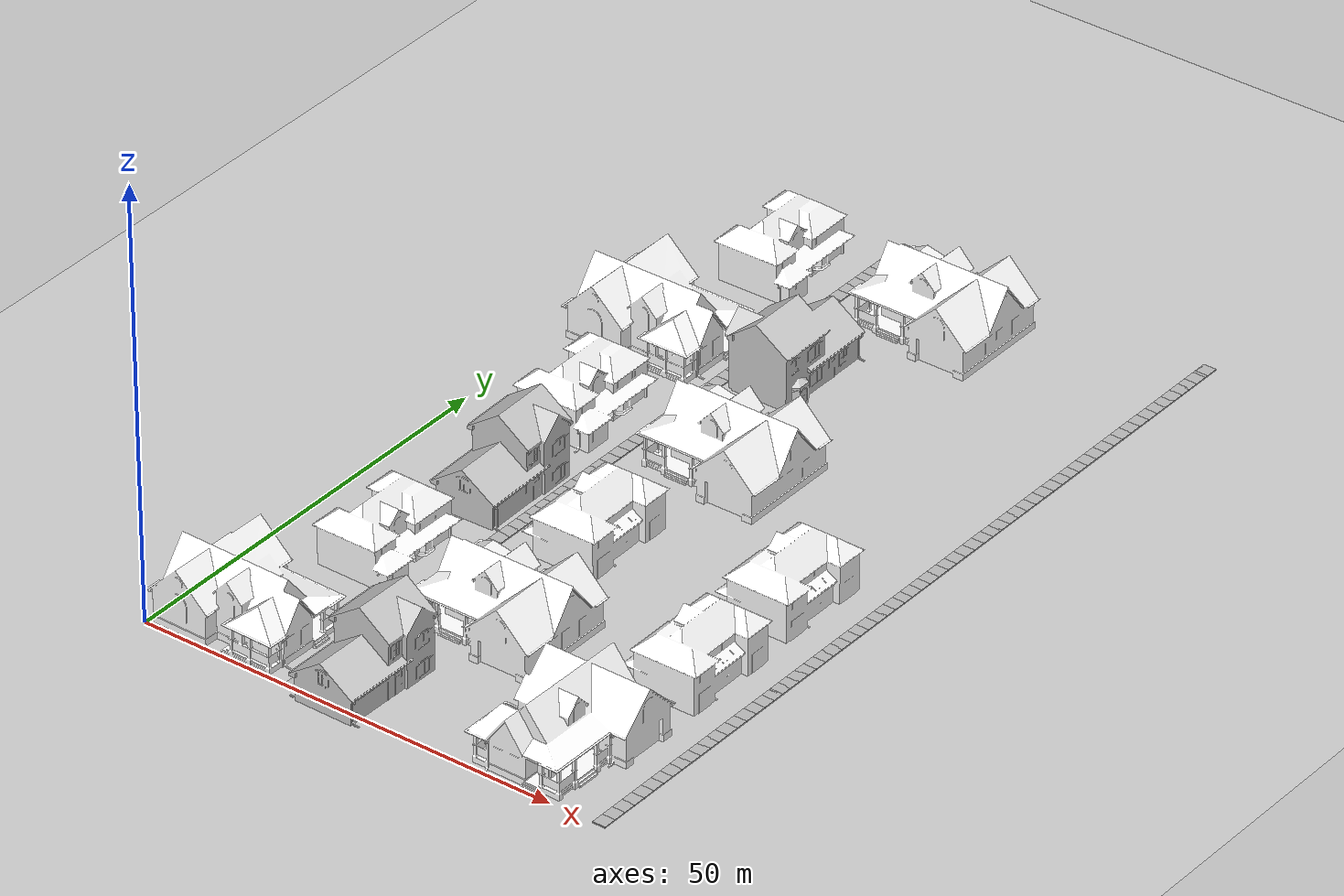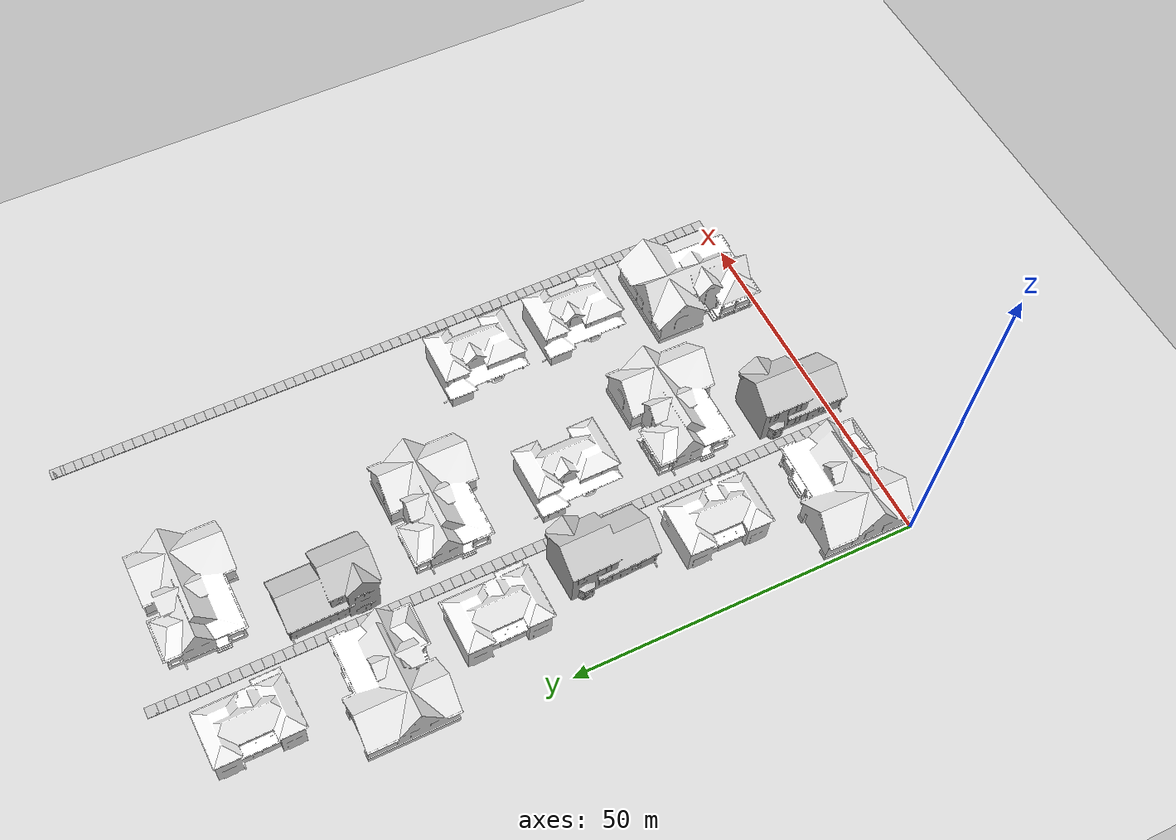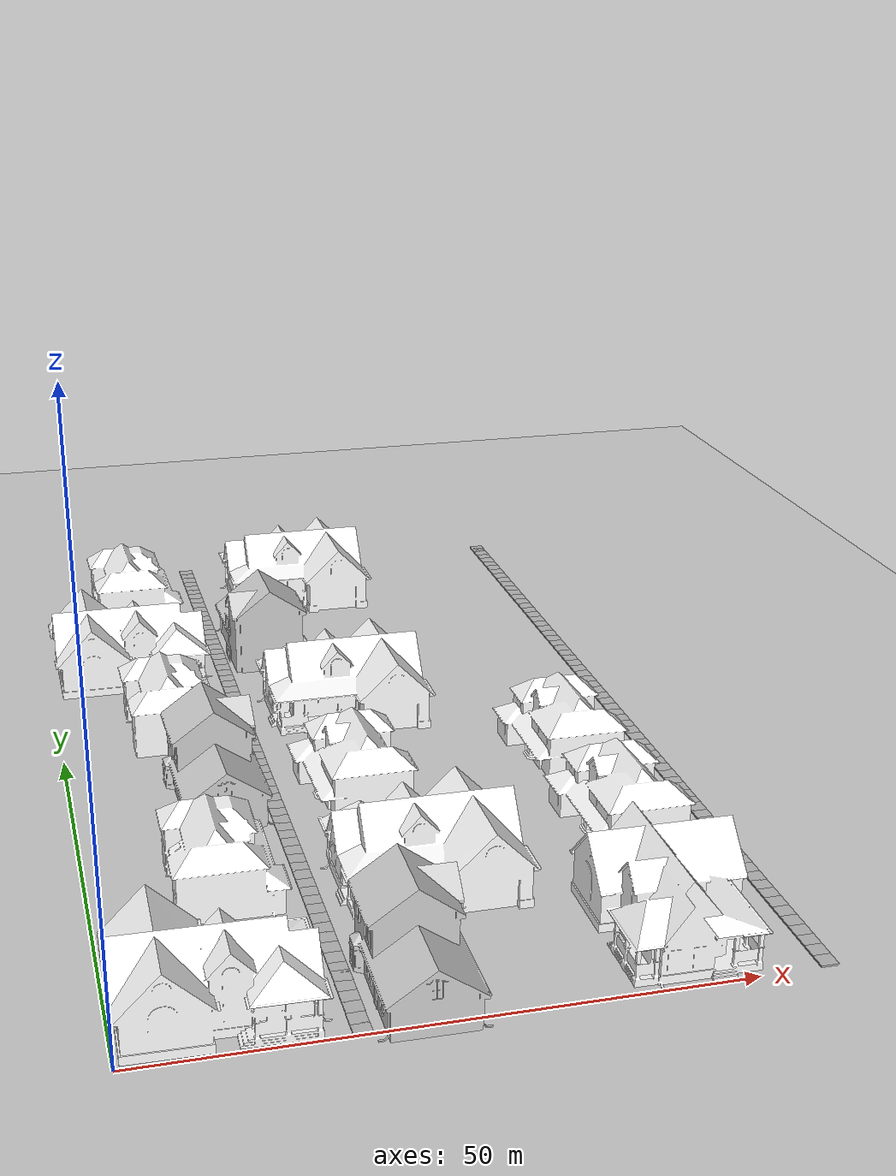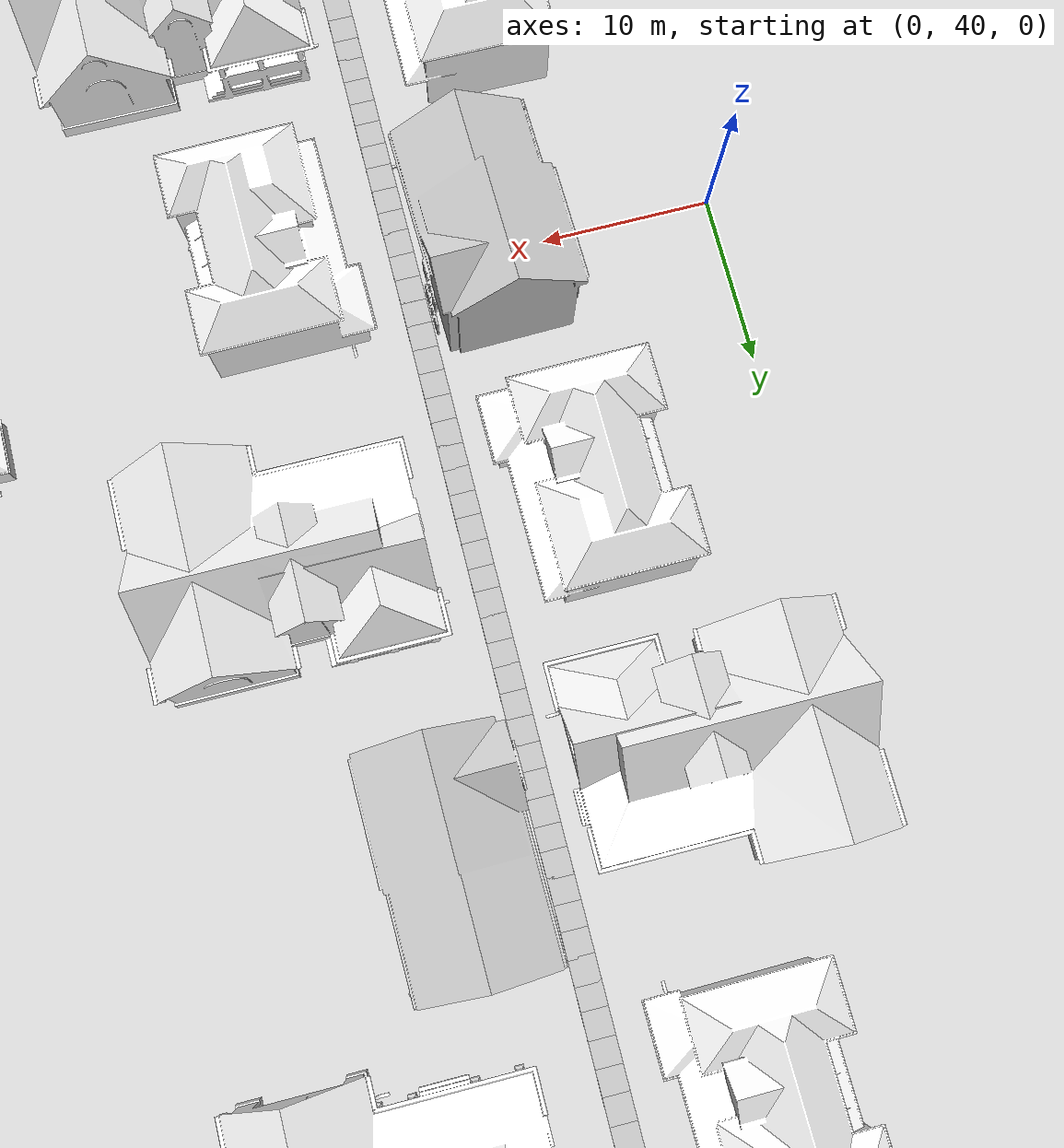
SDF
<sdf version="1.6">
 <world name="default">
  <light name="sun" type="directional">
   <pose>0 0 10 0 -0 0</pose>
   <diffuse>0.8 0.8 0.8 1</diffuse>
   <specular>0.2 0.2 0.2 1</specular>
   <attenuation>
    <range>1000</range>
    <constant>0.9</constant>
    <linear>0.01</linear>
    <quadratic>0.001</quadratic>
   </attenuation>
   <direction>-0.5 0.1 -0.9</direction>
  </light>
  <model name="ground_plane">
   <pose>50 50 0 0 -0 0</pose>
   <static>1</static>
   <link name="link">
    <collision name="collision">
     <geometry><plane><normal>0 0 1</normal><size>100 100</size></plane></geometry>
     <surface>
      <contact><collide_bitmask>65535</collide_bitmask></contact>
      <friction><ode><mu>100</mu><mu2>50</mu2></ode></friction>
     </surface>
    </collision>
    <visual name="visual">
     <cast_shadows>0</cast_shadows>
     <geometry><plane><normal>0 0 1</normal><size>100 100</size></plane></geometry>
     <material>
      <script><uri>file://media/materials/scripts/gazebo.material</uri><name>Gazebo/Grey</name></script>
     </material>
    </visual>
   </link>
  </model>
  <gravity>0 0 -9.8</gravity>
  <magnetic_field>6e-06 2.3e-05 -4.2e-05</magnetic_field>
  <atmosphere type="adiabatic"/>
  <physics name="default_physics" default="0" type="ode">
   <max_step_size>0.001</max_step_size>
   <real_time_factor>1</real_time_factor>
   <real_time_update_rate>1000</real_time_update_rate>
  </physics>
  <scene><ambient>0.4 0.4 0.4 1</ambient><background>0.7 0.7 0.7 1</background><shadows>1</shadows></scene>
  <audio><device>default</device></audio>
  <spherical_coordinates>
   <surface_model>EARTH_WGS84</surface_model>
   <latitude_deg>0</latitude_deg>
   <longitude_deg>0</longitude_deg>
   <elevation>0</elevation>
   <heading_deg>0</heading_deg>
  </spherical_coordinates>
  <model name="House 1">
   <static>1</static>
   <link name="link">
    <collision name="collision">
     <geometry><mesh><uri>model://house_1/meshes/house_1.dae</uri><scale>1.5 1.5 1.5</scale></mesh></geometry>
    </collision>
    <visual name="visual">
     <geometry><mesh><uri>model://house_1/meshes/house_1.dae</uri><scale>1.5 1.5 1.5</scale></mesh></geometry>
     <material>
      <script>
       <uri>model://house_1/materials/scripts</uri>
       <uri>model://house_1/materials/textures</uri>
       <name>House_1/Diffuse</name>
      </script>
      <shader type="normal_map_tangent_space"><normal_map>House_1_Normal.png</normal_map></shader>
     </material>
    </visual>
   </link>
   <pose>7.85395 6.03702 0 0 -0 3.12127</pose>
  </model>
  <model name="walkway_metal_straight">
   <static>1</static>
   <link name="link">
    <collision name="collision">
     <pose>0 0.762 0.076075 0 -0 0</pose>
     <geometry><box><size>1.524 1.524 0.15215</size></box></geometry>
    </collision>
    <visual name="visual">
     <geometry>
      <mesh><scale>0.001 0.001 0.001</scale><uri>model://walkway_metal_straight/meshes/mesh.obj</uri></mesh>
     </geometry>
    </visual>
   </link>
   <pose>18.2825 -0.072933 0 0 -0 0</pose>
  </model>
  <model name="walkway_metal_straight_0">
   <static>1</static>
   <link name="link">
    <collision name="collision">
     <pose>0 0.762 0.076075 0 -0 0</pose>
     <geometry><box><size>1.524 1.524 0.15215</size></box></geometry>
    </collision>
    <visual name="visual">
     <geometry>
      <mesh><scale>0.001 0.001 0.001</scale><uri>model://walkway_metal_straight/meshes/mesh.obj</uri></mesh>
     </geometry>
    </visual>
   </link>
   <pose>18.2758 1.21264 0 0 -0 0</pose>
  </model>
  <model name="walkway_metal_straight_1">
   <static>1</static>
   <link name="link">
    <collision name="collision">
     <pose>0 0.762 0.076075 0 -0 0</pose>
     <geometry><box><size>1.524 1.524 0.15215</size></box></geometry>
    </collision>
    <visual name="visual">
     <geometry>
      <mesh><scale>0.001 0.001 0.001</scale><uri>model://walkway_metal_straight/meshes/mesh.obj</uri></mesh>
     </geometry>
    </visual>
   </link>
   <pose>18.3018 2.69775 0 0 -0 0</pose>
  </model>
  <model name="walkway_metal_straight_2">
   <static>1</static>
   <link name="link">
    <collision name="collision">
     <pose>0 0.762 0.076075 0 -0 0</pose>
     <geometry><box><size>1.524 1.524 0.15215</size></box></geometry>
    </collision>
    <visual name="visual">
     <geometry>
      <mesh><scale>0.001 0.001 0.001</scale><uri>model://walkway_metal_straight/meshes/mesh.obj</uri></mesh>
     </geometry>
    </visual>
   </link>
   <pose>18.3024 4.11116 0 0 -0 0</pose>
  </model>
  <model name="walkway_metal_straight_3">
   <static>1</static>
   <link name="link">
    <collision name="collision">
     <pose>0 0.762 0.076075 0 -0 0</pose>
     <geometry><box><size>1.524 1.524 0.15215</size></box></geometry>
    </collision>
    <visual name="visual">
     <geometry>
      <mesh><scale>0.001 0.001 0.001</scale><uri>model://walkway_metal_straight/meshes/mesh.obj</uri></mesh>
     </geometry>
    </visual>
   </link>
   <pose>18.3048 5.48533 0 0 -0 0</pose>
  </model>
  <model name="walkway_metal_straight_4">
   <static>1</static>
   <link name="link">
    <collision name="collision">
     <pose>0 0.762 0.076075 0 -0 0</pose>
     <geometry><box><size>1.524 1.524 0.15215</size></box></geometry>
    </collision>
    <visual name="visual">
     <geometry>
      <mesh><scale>0.001 0.001 0.001</scale><uri>model://walkway_metal_straight/meshes/mesh.obj</uri></mesh>
     </geometry>
    </visual>
   </link>
   <pose>18.3241 6.94851 0 0 -0 0</pose>
  </model>
  <model name="walkway_metal_straight_5">
   <static>1</static>
   <link name="link">
    <collision name="collision">
     <pose>0 0.762 0.076075 0 -0 0</pose>
     <geometry><box><size>1.524 1.524 0.15215</size></box></geometry>
    </collision>
    <visual name="visual">
     <geometry>
      <mesh><scale>0.001 0.001 0.001</scale><uri>model://walkway_metal_straight/meshes/mesh.obj</uri></mesh>
     </geometry>
    </visual>
   </link>
   <pose>18.3171 8.13981 0 0 -0 0</pose>
  </model>
  <model name="walkway_metal_straight_6">
   <static>1</static>
   <link name="link">
    <collision name="collision">
     <pose>0 0.762 0.076075 0 -0 0</pose>
     <geometry><box><size>1.524 1.524 0.15215</size></box></geometry>
    </collision>
    <visual name="visual">
     <geometry>
      <mesh><scale>0.001 0.001 0.001</scale><uri>model://walkway_metal_straight/meshes/mesh.obj</uri></mesh>
     </geometry>
    </visual>
   </link>
   <pose>18.3157 9.63545 0 0 -0 0</pose>
  </model>
  <model name="walkway_metal_straight_7">
   <static>1</static>
   <link name="link">
    <collision name="collision">
     <pose>0 0.762 0.076075 0 -0 0</pose>
     <geometry><box><size>1.524 1.524 0.15215</size></box></geometry>
    </collision>
    <visual name="visual">
     <geometry>
      <mesh><scale>0.001 0.001 0.001</scale><uri>model://walkway_metal_straight/meshes/mesh.obj</uri></mesh>
     </geometry>
    </visual>
   </link>
   <pose>18.3179 11.1532 0 0 -0 0</pose>
  </model>
  <model name="walkway_metal_straight_8">
   <static>1</static>
   <link name="link">
    <collision name="collision">
     <pose>0 0.762 0.076075 0 -0 0</pose>
     <geometry><box><size>1.524 1.524 0.15215</size></box></geometry>
    </collision>
    <visual name="visual">
     <geometry>
      <mesh><scale>0.001 0.001 0.001</scale><uri>model://walkway_metal_straight/meshes/mesh.obj</uri></mesh>
     </geometry>
    </visual>
   </link>
   <pose>18.324 12.6444 0 0 -0 0</pose>
  </model>
  <model name="walkway_metal_straight_9">
   <static>1</static>
   <link name="link">
    <collision name="collision">
     <pose>0 0.762 0.076075 0 -0 0</pose>
     <geometry><box><size>1.524 1.524 0.15215</size></box></geometry>
    </collision>
    <visual name="visual">
     <geometry>
      <mesh><scale>0.001 0.001 0.001</scale><uri>model://walkway_metal_straight/meshes/mesh.obj</uri></mesh>
     </geometry>
    </visual>
   </link>
   <pose>18.3296 14.1195 0 0 -0 0</pose>
  </model>
  <model name="walkway_metal_straight_10">
   <static>1</static>
   <link name="link">
    <collision name="collision">
     <pose>0 0.762 0.076075 0 -0 0</pose>
     <geometry><box><size>1.524 1.524 0.15215</size></box></geometry>
    </collision>
    <visual name="visual">
     <geometry>
      <mesh><scale>0.001 0.001 0.001</scale><uri>model://walkway_metal_straight/meshes/mesh.obj</uri></mesh>
     </geometry>
    </visual>
   </link>
   <pose>18.3353 15.595 0 0 -0 0</pose>
  </model>
  <model name="walkway_metal_straight_11">
   <static>1</static>
   <link name="link">
    <collision name="collision">
     <pose>0 0.762 0.076075 0 -0 0</pose>
     <geometry><box><size>1.524 1.524 0.15215</size></box></geometry>
    </collision>
    <visual name="visual">
     <geometry>
      <mesh><scale>0.001 0.001 0.001</scale><uri>model://walkway_metal_straight/meshes/mesh.obj</uri></mesh>
     </geometry>
    </visual>
   </link>
   <pose>18.329 17.1047 0 0 -0 0</pose>
  </model>
  <model name="walkway_metal_straight_12">
   <static>1</static>
   <link name="link">
    <collision name="collision">
     <pose>0 0.762 0.076075 0 -0 0</pose>
     <geometry><box><size>1.524 1.524 0.15215</size></box></geometry>
    </collision>
    <visual name="visual">
     <geometry>
      <mesh><scale>0.001 0.001 0.001</scale><uri>model://walkway_metal_straight/meshes/mesh.obj</uri></mesh>
     </geometry>
    </visual>
   </link>
   <pose>18.3332 18.4995 0 0 -0 0</pose>
  </model>
  <model name="walkway_metal_straight_13">
   <static>1</static>
   <link name="link">
    <collision name="collision">
     <pose>0 0.762 0.076075 0 -0 0</pose>
     <geometry><box><size>1.524 1.524 0.15215</size></box></geometry>
    </collision>
    <visual name="visual">
     <geometry>
      <mesh><scale>0.001 0.001 0.001</scale><uri>model://walkway_metal_straight/meshes/mesh.obj</uri></mesh>
     </geometry>
    </visual>
   </link>
   <pose>18.338 19.9107 0 0 -0 0</pose>
  </model>
  <model name="walkway_metal_straight_14">
   <static>1</static>
   <link name="link">
    <collision name="collision">
     <pose>0 0.762 0.076075 0 -0 0</pose>
     <geometry><box><size>1.524 1.524 0.15215</size></box></geometry>
    </collision>
    <visual name="visual">
     <geometry>
      <mesh><scale>0.001 0.001 0.001</scale><uri>model://walkway_metal_straight/meshes/mesh.obj</uri></mesh>
     </geometry>
    </visual>
   </link>
   <pose>18.3372 21.3551 0 0 -0 0</pose>
  </model>
  <model name="walkway_metal_straight_15">
   <static>1</static>
   <link name="link">
    <collision name="collision">
     <pose>0 0.762 0.076075 0 -0 0</pose>
     <geometry><box><size>1.524 1.524 0.15215</size></box></geometry>
    </collision>
    <visual name="visual">
     <geometry>
      <mesh><scale>0.001 0.001 0.001</scale><uri>model://walkway_metal_straight/meshes/mesh.obj</uri></mesh>
     </geometry>
    </visual>
   </link>
   <pose>18.3337 22.8474 0 0 -0 0</pose>
  </model>
  <model name="walkway_metal_straight_16">
   <static>1</static>
   <link name="link">
    <collision name="collision">
     <pose>0 0.762 0.076075 0 -0 0</pose>
     <geometry><box><size>1.524 1.524 0.15215</size></box></geometry>
    </collision>
    <visual name="visual">
     <geometry>
      <mesh><scale>0.001 0.001 0.001</scale><uri>model://walkway_metal_straight/meshes/mesh.obj</uri></mesh>
     </geometry>
    </visual>
   </link>
   <pose>18.3477 24.1951 0 0 -0 0</pose>
  </model>
  <model name="walkway_metal_straight_17">
   <static>1</static>
   <link name="link">
    <collision name="collision">
     <pose>0 0.762 0.076075 0 -0 0</pose>
     <geometry><box><size>1.524 1.524 0.15215</size></box></geometry>
    </collision>
    <visual name="visual">
     <geometry>
      <mesh><scale>0.001 0.001 0.001</scale><uri>model://walkway_metal_straight/meshes/mesh.obj</uri></mesh>
     </geometry>
    </visual>
   </link>
   <pose>18.345 25.6384 0 0 -0 0</pose>
  </model>
  <model name="walkway_metal_straight_18">
   <static>1</static>
   <link name="link">
    <collision name="collision">
     <pose>0 0.762 0.076075 0 -0 0</pose>
     <geometry><box><size>1.524 1.524 0.15215</size></box></geometry>
    </collision>
    <visual name="visual">
     <geometry>
      <mesh><scale>0.001 0.001 0.001</scale><uri>model://walkway_metal_straight/meshes/mesh.obj</uri></mesh>
     </geometry>
    </visual>
   </link>
   <pose>18.3364 27.1272 0 0 -0 0</pose>
  </model>
  <model name="walkway_metal_straight_19">
   <static>1</static>
   <link name="link">
    <collision name="collision">
     <pose>0 0.762 0.076075 0 -0 0</pose>
     <geometry><box><size>1.524 1.524 0.15215</size></box></geometry>
    </collision>
    <visual name="visual">
     <geometry>
      <mesh><scale>0.001 0.001 0.001</scale><uri>model://walkway_metal_straight/meshes/mesh.obj</uri></mesh>
     </geometry>
    </visual>
   </link>
   <pose>18.3402 28.6079 0 0 -0 0</pose>
  </model>
  <model name="walkway_metal_straight_20">
   <static>1</static>
   <link name="link">
    <collision name="collision">
     <pose>0 0.762 0.076075 0 -0 0</pose>
     <geometry><box><size>1.524 1.524 0.15215</size></box></geometry>
    </collision>
    <visual name="visual">
     <geometry>
      <mesh><scale>0.001 0.001 0.001</scale><uri>model://walkway_metal_straight/meshes/mesh.obj</uri></mesh>
     </geometry>
    </visual>
   </link>
   <pose>18.3445 30.0526 0 0 -0 0</pose>
  </model>
  <model name="walkway_metal_straight_21">
   <static>1</static>
   <link name="link">
    <collision name="collision">
     <pose>0 0.762 0.076075 0 -0 0</pose>
     <geometry><box><size>1.524 1.524 0.15215</size></box></geometry>
    </collision>
    <visual name="visual">
     <geometry>
      <mesh><scale>0.001 0.001 0.001</scale><uri>model://walkway_metal_straight/meshes/mesh.obj</uri></mesh>
     </geometry>
    </visual>
   </link>
   <pose>18.337 31.5447 0 0 -0 0</pose>
  </model>
  <model name="walkway_metal_straight_22">
   <static>1</static>
   <link name="link">
    <collision name="collision">
     <pose>0 0.762 0.076075 0 -0 0</pose>
     <geometry><box><size>1.524 1.524 0.15215</size></box></geometry>
    </collision>
    <visual name="visual">
     <geometry>
      <mesh><scale>0.001 0.001 0.001</scale><uri>model://walkway_metal_straight/meshes/mesh.obj</uri></mesh>
     </geometry>
    </visual>
   </link>
   <pose>18.3409 32.9529 0 0 -0 0</pose>
  </model>
  <model name="walkway_metal_straight_23">
   <static>1</static>
   <link name="link">
    <collision name="collision">
     <pose>0 0.762 0.076075 0 -0 0</pose>
     <geometry><box><size>1.524 1.524 0.15215</size></box></geometry>
    </collision>
    <visual name="visual">
     <geometry>
      <mesh><scale>0.001 0.001 0.001</scale><uri>model://walkway_metal_straight/meshes/mesh.obj</uri></mesh>
     </geometry>
    </visual>
   </link>
   <pose>18.3386 34.3966 0 0 -0 0</pose>
  </model>
  <model name="walkway_metal_straight_24">
   <static>1</static>
   <link name="link">
    <collision name="collision">
     <pose>0 0.762 0.076075 0 -0 0</pose>
     <geometry><box><size>1.524 1.524 0.15215</size></box></geometry>
    </collision>
    <visual name="visual">
     <geometry>
      <mesh><scale>0.001 0.001 0.001</scale><uri>model://walkway_metal_straight/meshes/mesh.obj</uri></mesh>
     </geometry>
    </visual>
   </link>
   <pose>18.3354 35.8409 0 0 -0 0</pose>
  </model>
  <model name="walkway_metal_straight_25">
   <static>1</static>
   <link name="link">
    <collision name="collision">
     <pose>0 0.762 0.076075 0 -0 0</pose>
     <geometry><box><size>1.524 1.524 0.15215</size></box></geometry>
    </collision>
    <visual name="visual">
     <geometry>
      <mesh><scale>0.001 0.001 0.001</scale><uri>model://walkway_metal_straight/meshes/mesh.obj</uri></mesh>
     </geometry>
    </visual>
   </link>
   <pose>18.3245 37.2528 0 0 -0 0</pose>
  </model>
  <model name="walkway_metal_straight_26">
   <static>1</static>
   <link name="link">
    <collision name="collision">
     <pose>0 0.762 0.076075 0 -0 0</pose>
     <geometry><box><size>1.524 1.524 0.15215</size></box></geometry>
    </collision>
    <visual name="visual">
     <geometry>
      <mesh><scale>0.001 0.001 0.001</scale><uri>model://walkway_metal_straight/meshes/mesh.obj</uri></mesh>
     </geometry>
    </visual>
   </link>
   <pose>18.3287 38.7686 0 0 -0 0</pose>
  </model>
  <model name="walkway_metal_straight_27">
   <static>1</static>
   <link name="link">
    <collision name="collision">
     <pose>0 0.762 0.076075 0 -0 0</pose>
     <geometry><box><size>1.524 1.524 0.15215</size></box></geometry>
    </collision>
    <visual name="visual">
     <geometry>
      <mesh><scale>0.001 0.001 0.001</scale><uri>model://walkway_metal_straight/meshes/mesh.obj</uri></mesh>
     </geometry>
    </visual>
   </link>
   <pose>18.3226 40.2752 0 0 -0 0</pose>
  </model>
  <model name="walkway_metal_straight_28">
   <static>1</static>
   <link name="link">
    <collision name="collision">
     <pose>0 0.762 0.076075 0 -0 0</pose>
     <geometry><box><size>1.524 1.524 0.15215</size></box></geometry>
    </collision>
    <visual name="visual">
     <geometry>
      <mesh><scale>0.001 0.001 0.001</scale><uri>model://walkway_metal_straight/meshes/mesh.obj</uri></mesh>
     </geometry>
    </visual>
   </link>
   <pose>18.3267 41.7464 0 0 -0 0</pose>
  </model>
  <model name="walkway_metal_straight_29">
   <static>1</static>
   <link name="link">
    <collision name="collision">
     <pose>0 0.762 0.076075 0 -0 0</pose>
     <geometry><box><size>1.524 1.524 0.15215</size></box></geometry>
    </collision>
    <visual name="visual">
     <geometry>
      <mesh><scale>0.001 0.001 0.001</scale><uri>model://walkway_metal_straight/meshes/mesh.obj</uri></mesh>
     </geometry>
    </visual>
   </link>
   <pose>18.331 43.2478 0 0 -0 0</pose>
  </model>
  <model name="walkway_metal_straight_30">
   <static>1</static>
   <link name="link">
    <collision name="collision">
     <pose>0 0.762 0.076075 0 -0 0</pose>
     <geometry><box><size>1.524 1.524 0.15215</size></box></geometry>
    </collision>
    <visual name="visual">
     <geometry>
      <mesh><scale>0.001 0.001 0.001</scale><uri>model://walkway_metal_straight/meshes/mesh.obj</uri></mesh>
     </geometry>
    </visual>
   </link>
   <pose>18.3351 44.7496 0 0 -0 0</pose>
  </model>
  <model name="walkway_metal_straight_31">
   <static>1</static>
   <link name="link">
    <collision name="collision">
     <pose>0 0.762 0.076075 0 -0 0</pose>
     <geometry><box><size>1.524 1.524 0.15215</size></box></geometry>
    </collision>
    <visual name="visual">
     <geometry>
      <mesh><scale>0.001 0.001 0.001</scale><uri>model://walkway_metal_straight/meshes/mesh.obj</uri></mesh>
     </geometry>
    </visual>
   </link>
   <pose>18.3385 46.2534 0 0 -0 0</pose>
  </model>
  <model name="walkway_metal_straight_32">
   <static>1</static>
   <link name="link">
    <collision name="collision">
     <pose>0 0.762 0.076075 0 -0 0</pose>
     <geometry><box><size>1.524 1.524 0.15215</size></box></geometry>
    </collision>
    <visual name="visual">
     <geometry>
      <mesh><scale>0.001 0.001 0.001</scale><uri>model://walkway_metal_straight/meshes/mesh.obj</uri></mesh>
     </geometry>
    </visual>
   </link>
   <pose>18.3427 47.7684 0 0 -0 0</pose>
  </model>
  <model name="walkway_metal_straight_33">
   <static>1</static>
   <link name="link">
    <collision name="collision">
     <pose>0 0.762 0.076075 0 -0 0</pose>
     <geometry><box><size>1.524 1.524 0.15215</size></box></geometry>
    </collision>
    <visual name="visual">
     <geometry>
      <mesh><scale>0.001 0.001 0.001</scale><uri>model://walkway_metal_straight/meshes/mesh.obj</uri></mesh>
     </geometry>
    </visual>
   </link>
   <pose>18.3468 49.2696 0 0 -0 0</pose>
  </model>
  <model name="walkway_metal_straight_34">
   <static>1</static>
   <link name="link">
    <collision name="collision">
     <pose>0 0.762 0.076075 0 -0 0</pose>
     <geometry><box><size>1.524 1.524 0.15215</size></box></geometry>
    </collision>
    <visual name="visual">
     <geometry>
      <mesh><scale>0.001 0.001 0.001</scale><uri>model://walkway_metal_straight/meshes/mesh.obj</uri></mesh>
     </geometry>
    </visual>
   </link>
   <pose>18.3508 50.7068 0 0 -0 0</pose>
  </model>
  <model name="walkway_metal_straight_35">
   <static>1</static>
   <link name="link">
    <collision name="collision">
     <pose>0 0.762 0.076075 0 -0 0</pose>
     <geometry><box><size>1.524 1.524 0.15215</size></box></geometry>
    </collision>
    <visual name="visual">
     <geometry>
      <mesh><scale>0.001 0.001 0.001</scale><uri>model://walkway_metal_straight/meshes/mesh.obj</uri></mesh>
     </geometry>
    </visual>
   </link>
   <pose>18.3547 52.1825 0 0 -0 0</pose>
  </model>
  <model name="walkway_metal_straight_36">
   <static>1</static>
   <link name="link">
    <collision name="collision">
     <pose>0 0.762 0.076075 0 -0 0</pose>
     <geometry><box><size>1.524 1.524 0.15215</size></box></geometry>
    </collision>
    <visual name="visual">
     <geometry>
      <mesh><scale>0.001 0.001 0.001</scale><uri>model://walkway_metal_straight/meshes/mesh.obj</uri></mesh>
     </geometry>
    </visual>
   </link>
   <pose>18.3625 53.6972 0 0 -0 0</pose>
  </model>
  <model name="walkway_metal_straight_37">
   <static>1</static>
   <link name="link">
    <collision name="collision">
     <pose>0 0.762 0.076075 0 -0 0</pose>
     <geometry><box><size>1.524 1.524 0.15215</size></box></geometry>
    </collision>
    <visual name="visual">
     <geometry>
      <mesh><scale>0.001 0.001 0.001</scale><uri>model://walkway_metal_straight/meshes/mesh.obj</uri></mesh>
     </geometry>
    </visual>
   </link>
   <pose>18.3663 55.1075 0 0 -0 0</pose>
  </model>
  <model name="walkway_metal_straight_38">
   <static>1</static>
   <link name="link">
    <collision name="collision">
     <pose>0 0.762 0.076075 0 -0 0</pose>
     <geometry><box><size>1.524 1.524 0.15215</size></box></geometry>
    </collision>
    <visual name="visual">
     <geometry>
      <mesh><scale>0.001 0.001 0.001</scale><uri>model://walkway_metal_straight/meshes/mesh.obj</uri></mesh>
     </geometry>
    </visual>
   </link>
   <pose>18.3704 56.6101 0 0 -0 0</pose>
  </model>
  <model name="walkway_metal_straight_39">
   <static>1</static>
   <link name="link">
    <collision name="collision">
     <pose>0 0.762 0.076075 0 -0 0</pose>
     <geometry><box><size>1.524 1.524 0.15215</size></box></geometry>
    </collision>
    <visual name="visual">
     <geometry>
      <mesh><scale>0.001 0.001 0.001</scale><uri>model://walkway_metal_straight/meshes/mesh.obj</uri></mesh>
     </geometry>
    </visual>
   </link>
   <pose>18.3744 58.0331 0 0 -0 0</pose>
  </model>
  <model name="walkway_metal_straight_40">
   <static>1</static>
   <link name="link">
    <collision name="collision">
     <pose>0 0.762 0.076075 0 -0 0</pose>
     <geometry><box><size>1.524 1.524 0.15215</size></box></geometry>
    </collision>
    <visual name="visual">
     <geometry>
      <mesh><scale>0.001 0.001 0.001</scale><uri>model://walkway_metal_straight/meshes/mesh.obj</uri></mesh>
     </geometry>
    </visual>
   </link>
   <pose>18.3739 59.4805 0 0 -0 0</pose>
  </model>
  <model name="walkway_metal_straight_41">
   <static>1</static>
   <link name="link">
    <collision name="collision">
     <pose>0 0.762 0.076075 0 -0 0</pose>
     <geometry><box><size>1.524 1.524 0.15215</size></box></geometry>
    </collision>
    <visual name="visual">
     <geometry>
      <mesh><scale>0.001 0.001 0.001</scale><uri>model://walkway_metal_straight/meshes/mesh.obj</uri></mesh>
     </geometry>
    </visual>
   </link>
   <pose>18.3743 60.9514 0 0 -0 0</pose>
  </model>
  <model name="walkway_metal_straight_42">
   <static>1</static>
   <link name="link">
    <collision name="collision">
     <pose>0 0.762 0.076075 0 -0 0</pose>
     <geometry><box><size>1.524 1.524 0.15215</size></box></geometry>
    </collision>
    <visual name="visual">
     <geometry>
      <mesh><scale>0.001 0.001 0.001</scale><uri>model://walkway_metal_straight/meshes/mesh.obj</uri></mesh>
     </geometry>
    </visual>
   </link>
   <pose>18.3759 62.3786 0 0 -0 0</pose>
  </model>
  <model name="walkway_metal_straight_43">
   <static>1</static>
   <link name="link">
    <collision name="collision">
     <pose>0 0.762 0.076075 0 -0 0</pose>
     <geometry><box><size>1.524 1.524 0.15215</size></box></geometry>
    </collision>
    <visual name="visual">
     <geometry>
      <mesh><scale>0.001 0.001 0.001</scale><uri>model://walkway_metal_straight/meshes/mesh.obj</uri></mesh>
     </geometry>
    </visual>
   </link>
   <pose>18.3772 63.8674 0 0 -0 0</pose>
  </model>
  <model name="walkway_metal_straight_44">
   <static>1</static>
   <link name="link">
    <collision name="collision">
     <pose>0 0.762 0.076075 0 -0 0</pose>
     <geometry><box><size>1.524 1.524 0.15215</size></box></geometry>
    </collision>
    <visual name="visual">
     <geometry>
      <mesh><scale>0.001 0.001 0.001</scale><uri>model://walkway_metal_straight/meshes/mesh.obj</uri></mesh>
     </geometry>
    </visual>
   </link>
   <pose>18.3815 65.3735 0 0 -0 0</pose>
  </model>
  <model name="walkway_metal_straight_45">
   <static>1</static>
   <link name="link">
    <collision name="collision">
     <pose>0 0.762 0.076075 0 -0 0</pose>
     <geometry><box><size>1.524 1.524 0.15215</size></box></geometry>
    </collision>
    <visual name="visual">
     <geometry>
      <mesh><scale>0.001 0.001 0.001</scale><uri>model://walkway_metal_straight/meshes/mesh.obj</uri></mesh>
     </geometry>
    </visual>
   </link>
   <pose>18.3856 66.8805 0 0 -0 0</pose>
  </model>
  <model name="walkway_metal_straight_46">
   <static>1</static>
   <link name="link">
    <collision name="collision">
     <pose>0 0.762 0.076075 0 -0 0</pose>
     <geometry><box><size>1.524 1.524 0.15215</size></box></geometry>
    </collision>
    <visual name="visual">
     <geometry>
      <mesh><scale>0.001 0.001 0.001</scale><uri>model://walkway_metal_straight/meshes/mesh.obj</uri></mesh>
     </geometry>
    </visual>
   </link>
   <pose>18.3831 68.3481 0 0 -0 0</pose>
  </model>
  <model name="walkway_metal_straight_47">
   <static>1</static>
   <link name="link">
    <collision name="collision">
     <pose>0 0.762 0.076075 0 -0 0</pose>
     <geometry><box><size>1.524 1.524 0.15215</size></box></geometry>
    </collision>
    <visual name="visual">
     <geometry>
      <mesh><scale>0.001 0.001 0.001</scale><uri>model://walkway_metal_straight/meshes/mesh.obj</uri></mesh>
     </geometry>
    </visual>
   </link>
   <pose>18.3874 69.8743 0 0 -0 0</pose>
  </model>
  <model name="walkway_metal_straight_48">
   <static>1</static>
   <link name="link">
    <collision name="collision">
     <pose>0 0.762 0.076075 0 -0 0</pose>
     <geometry><box><size>1.524 1.524 0.15215</size></box></geometry>
    </collision>
    <visual name="visual">
     <geometry>
      <mesh><scale>0.001 0.001 0.001</scale><uri>model://walkway_metal_straight/meshes/mesh.obj</uri></mesh>
     </geometry>
    </visual>
   </link>
   <pose>18.3874 71.4001 0 0 -0 0</pose>
  </model>
  <model name="walkway_metal_straight_49">
   <static>1</static>
   <link name="link">
    <collision name="collision">
     <pose>0 0.762 0.076075 0 -0 0</pose>
     <geometry><box><size>1.524 1.524 0.15215</size></box></geometry>
    </collision>
    <visual name="visual">
     <geometry>
      <mesh><scale>0.001 0.001 0.001</scale><uri>model://walkway_metal_straight/meshes/mesh.obj</uri></mesh>
     </geometry>
    </visual>
   </link>
   <pose>18.3915 72.8605 0 0 -0 0</pose>
  </model>
  <model name="walkway_metal_straight_50">
   <static>1</static>
   <link name="link">
    <collision name="collision">
     <pose>0 0.762 0.076075 0 -0 0</pose>
     <geometry><box><size>1.524 1.524 0.15215</size></box></geometry>
    </collision>
    <visual name="visual">
     <geometry>
      <mesh><scale>0.001 0.001 0.001</scale><uri>model://walkway_metal_straight/meshes/mesh.obj</uri></mesh>
     </geometry>
    </visual>
   </link>
   <pose>18.3838 74.2724 0 0 -0 0</pose>
  </model>
  <model name="walkway_metal_straight_51">
   <static>1</static>
   <link name="link">
    <collision name="collision">
     <pose>0 0.762 0.076075 0 -0 0</pose>
     <geometry><box><size>1.524 1.524 0.15215</size></box></geometry>
    </collision>
    <visual name="visual">
     <geometry>
      <mesh><scale>0.001 0.001 0.001</scale><uri>model://walkway_metal_straight/meshes/mesh.obj</uri></mesh>
     </geometry>
    </visual>
   </link>
   <pose>18.38 75.6675 0 0 -0 0</pose>
  </model>
  <model name="walkway_metal_straight_52">
   <static>1</static>
   <link name="link">
    <collision name="collision">
     <pose>0 0.762 0.076075 0 -0 0</pose>
     <geometry><box><size>1.524 1.524 0.15215</size></box></geometry>
    </collision>
    <visual name="visual">
     <geometry>
      <mesh><scale>0.001 0.001 0.001</scale><uri>model://walkway_metal_straight/meshes/mesh.obj</uri></mesh>
     </geometry>
    </visual>
   </link>
   <pose>18.3765 77.1832 0 0 -0 0</pose>
  </model>
  <model name="walkway_metal_straight_53">
   <static>1</static>
   <link name="link">
    <collision name="collision">
     <pose>0 0.762 0.076075 0 -0 0</pose>
     <geometry><box><size>1.524 1.524 0.15215</size></box></geometry>
    </collision>
    <visual name="visual">
     <geometry>
      <mesh><scale>0.001 0.001 0.001</scale><uri>model://walkway_metal_straight/meshes/mesh.obj</uri></mesh>
     </geometry>
    </visual>
   </link>
   <pose>18.3821 78.6177 0 0 -0 0</pose>
  </model>
  <model name="walkway_metal_straight_54">
   <static>1</static>
   <link name="link">
    <collision name="collision">
     <pose>0 0.762 0.076075 0 -0 0</pose>
     <geometry><box><size>1.524 1.524 0.15215</size></box></geometry>
    </collision>
    <visual name="visual">
     <geometry>
      <mesh><scale>0.001 0.001 0.001</scale><uri>model://walkway_metal_straight/meshes/mesh.obj</uri></mesh>
     </geometry>
    </visual>
   </link>
   <pose>18.3854 80.0339 0 0 -0 0</pose>
  </model>
  <model name="walkway_metal_straight_55">
   <static>1</static>
   <link name="link">
    <collision name="collision">
     <pose>0 0.762 0.076075 0 -0 0</pose>
     <geometry><box><size>1.524 1.524 0.15215</size></box></geometry>
    </collision>
    <visual name="visual">
     <geometry>
      <mesh><scale>0.001 0.001 0.001</scale><uri>model://walkway_metal_straight/meshes/mesh.obj</uri></mesh>
     </geometry>
    </visual>
   </link>
   <pose>18.3895 81.4542 0 0 -0 0</pose>
  </model>
  <model name="walkway_metal_straight_56">
   <static>1</static>
   <link name="link">
    <collision name="collision">
     <pose>0 0.762 0.076075 0 -0 0</pose>
     <geometry><box><size>1.524 1.524 0.15215</size></box></geometry>
    </collision>
    <visual name="visual">
     <geometry>
      <mesh><scale>0.001 0.001 0.001</scale><uri>model://walkway_metal_straight/meshes/mesh.obj</uri></mesh>
     </geometry>
    </visual>
   </link>
   <pose>18.3931 82.852 0 0 -0 0</pose>
  </model>
  <model name="walkway_metal_straight_57">
   <static>1</static>
   <link name="link">
    <collision name="collision">
     <pose>0 0.762 0.076075 0 -0 0</pose>
     <geometry><box><size>1.524 1.524 0.15215</size></box></geometry>
    </collision>
    <visual name="visual">
     <geometry>
      <mesh><scale>0.001 0.001 0.001</scale><uri>model://walkway_metal_straight/meshes/mesh.obj</uri></mesh>
     </geometry>
    </visual>
   </link>
   <pose>18.3972 84.3296 0 0 -0 0</pose>
  </model>
  <model name="walkway_metal_straight_58">
   <static>1</static>
   <link name="link">
    <collision name="collision">
     <pose>0 0.762 0.076075 0 -0 0</pose>
     <geometry><box><size>1.524 1.524 0.15215</size></box></geometry>
    </collision>
    <visual name="visual">
     <geometry>
      <mesh><scale>0.001 0.001 0.001</scale><uri>model://walkway_metal_straight/meshes/mesh.obj</uri></mesh>
     </geometry>
    </visual>
   </link>
   <pose>18.4013 85.7673 0 0 -0 0</pose>
  </model>
  <model name="walkway_metal_straight_59">
   <static>1</static>
   <link name="link">
    <collision name="collision">
     <pose>0 0.762 0.076075 0 -0 0</pose>
     <geometry><box><size>1.524 1.524 0.15215</size></box></geometry>
    </collision>
    <visual name="visual">
     <geometry>
      <mesh><scale>0.001 0.001 0.001</scale><uri>model://walkway_metal_straight/meshes/mesh.obj</uri></mesh>
     </geometry>
    </visual>
   </link>
   <pose>18.4035 87.2813 0 0 -0 0</pose>
  </model>
  <model name="walkway_metal_straight_60">
   <static>1</static>
   <link name="link">
    <collision name="collision">
     <pose>0 0.762 0.076075 0 -0 0</pose>
     <geometry><box><size>1.524 1.524 0.15215</size></box></geometry>
    </collision>
    <visual name="visual">
     <geometry>
      <mesh><scale>0.001 0.001 0.001</scale><uri>model://walkway_metal_straight/meshes/mesh.obj</uri></mesh>
     </geometry>
    </visual>
   </link>
   <pose>18.4076 88.7784 0 0 -0 0</pose>
  </model>
  <model name="walkway_metal_straight_61">
   <static>1</static>
   <link name="link">
    <collision name="collision">
     <pose>0 0.762 0.076075 0 -0 0</pose>
     <geometry><box><size>1.524 1.524 0.15215</size></box></geometry>
    </collision>
    <visual name="visual">
     <geometry>
      <mesh><scale>0.001 0.001 0.001</scale><uri>model://walkway_metal_straight/meshes/mesh.obj</uri></mesh>
     </geometry>
    </visual>
   </link>
   <pose>18.4114 90.2161 0 0 -0 0</pose>
  </model>
  <model name="walkway_metal_straight_62">
   <static>1</static>
   <link name="link">
    <collision name="collision">
     <pose>0 0.762 0.076075 0 -0 0</pose>
     <geometry><box><size>1.524 1.524 0.15215</size></box></geometry>
    </collision>
    <visual name="visual">
     <geometry>
      <mesh><scale>0.001 0.001 0.001</scale><uri>model://walkway_metal_straight/meshes/mesh.obj</uri></mesh>
     </geometry>
    </visual>
   </link>
   <pose>18.415 91.577 0 0 -0 0</pose>
  </model>
  <model name="walkway_metal_straight_63">
   <static>1</static>
   <link name="link">
    <collision name="collision">
     <pose>0 0.762 0.076075 0 -0 0</pose>
     <geometry><box><size>1.524 1.524 0.15215</size></box></geometry>
    </collision>
    <visual name="visual">
     <geometry>
      <mesh><scale>0.001 0.001 0.001</scale><uri>model://walkway_metal_straight/meshes/mesh.obj</uri></mesh>
     </geometry>
    </visual>
   </link>
   <pose>18.4191 92.9368 0 0 -0 0</pose>
  </model>
  <model name="walkway_metal_straight_64">
   <static>1</static>
   <link name="link">
    <collision name="collision">
     <pose>0 0.762 0.076075 0 -0 0</pose>
     <geometry><box><size>1.524 1.524 0.15215</size></box></geometry>
    </collision>
    <visual name="visual">
     <geometry>
      <mesh><scale>0.001 0.001 0.001</scale><uri>model://walkway_metal_straight/meshes/mesh.obj</uri></mesh>
     </geometry>
    </visual>
   </link>
   <pose>18.4227 94.2966 0 0 -0 0</pose>
  </model>
  <model name="walkway_metal_straight_65">
   <static>1</static>
   <link name="link">
    <collision name="collision">
     <pose>0 0.762 0.076075 0 -0 0</pose>
     <geometry><box><size>1.524 1.524 0.15215</size></box></geometry>
    </collision>
    <visual name="visual">
     <geometry>
      <mesh><scale>0.001 0.001 0.001</scale><uri>model://walkway_metal_straight/meshes/mesh.obj</uri></mesh>
     </geometry>
    </visual>
   </link>
   <pose>18.4268 95.7938 0 0 -0 0</pose>
  </model>
  <model name="walkway_metal_straight_66">
   <static>1</static>
   <link name="link">
    <collision name="collision">
     <pose>0 0.762 0.076075 0 -0 0</pose>
     <geometry><box><size>1.524 1.524 0.15215</size></box></geometry>
    </collision>
    <visual name="visual">
     <geometry>
      <mesh><scale>0.001 0.001 0.001</scale><uri>model://walkway_metal_straight/meshes/mesh.obj</uri></mesh>
     </geometry>
    </visual>
   </link>
   <pose>18.4306 97.1741 0 0 -0 0</pose>
  </model>
  <model name="walkway_metal_straight_67">
   <static>1</static>
   <link name="link">
    <collision name="collision">
     <pose>0 0.762 0.076075 0 -0 0</pose>
     <geometry><box><size>1.524 1.524 0.15215</size></box></geometry>
    </collision>
    <visual name="visual">
     <geometry>
      <mesh><scale>0.001 0.001 0.001</scale><uri>model://walkway_metal_straight/meshes/mesh.obj</uri></mesh>
     </geometry>
    </visual>
   </link>
   <pose>18.4339 98.3782 0 0 -0 0</pose>
  </model>
  <model name="House 2">
   <static>1</static>
   <link name="link">
    <collision name="collision">
     <geometry><mesh><uri>model://house_2/meshes/house_2.dae</uri><scale>1.5 1.5 1.5</scale></mesh></geometry>
    </collision>
    <visual name="visual">
     <geometry><mesh><uri>model://house_2/meshes/house_2.dae</uri><scale>1.5 1.5 1.5</scale></mesh></geometry>
     <material>
      <script>
       <uri>model://house_2/materials/scripts</uri>
       <uri>model://house_2/materials/textures</uri>
       <uri>model://house_1/materials/textures</uri>
       <name>House_2/Diffuse</name>
      </script>
      <shader type="normal_map_tangent_space">
       <normal_map>model://house_1/materials/textures/House_1_Normal.png</normal_map>
      </shader>
     </material>
    </visual>
   </link>
   <pose>10.7578 24.6942 0 0 0 -1.58213</pose>
  </model>
  <model name="House 3">
   <static>1</static>
   <link name="link">
    <collision name="collision">
     <geometry><mesh><uri>model://house_3/meshes/house_3.dae</uri><scale>1.5 1.5 1.5</scale></mesh></geometry>
    </collision>
    <visual name="visual">
     <geometry><mesh><uri>model://house_3/meshes/house_3.dae</uri><scale>1.5 1.5 1.5</scale></mesh></geometry>
     <material>
      <script>
       <uri>model://house_3/materials/scripts</uri>
       <uri>model://house_3/materials/textures</uri>
       <uri>model://house_1/materials/textures</uri>
       <name>House_3/Diffuse</name>
      </script>
      <shader type="normal_map_tangent_space">
       <normal_map>model://house_1/materials/textures/House_1_Normal.png</normal_map>
      </shader>
     </material>
    </visual>
   </link>
   <pose>13.2913 38.655 0 0 0 -1.54825</pose>
  </model>
  <model name="House 2_0">
   <static>1</static>
   <link name="link">
    <collision name="collision">
     <geometry><mesh><uri>model://house_2/meshes/house_2.dae</uri><scale>1.5 1.5 1.5</scale></mesh></geometry>
    </collision>
    <visual name="visual">
     <geometry><mesh><uri>model://house_2/meshes/house_2.dae</uri><scale>1.5 1.5 1.5</scale></mesh></geometry>
     <material>
      <script>
       <uri>model://house_2/materials/scripts</uri>
       <uri>model://house_2/materials/textures</uri>
       <uri>model://house_1/materials/textures</uri>
       <name>House_2/Diffuse</name>
      </script>
      <shader type="normal_map_tangent_space">
       <normal_map>model://house_1/materials/textures/House_1_Normal.png</normal_map>
      </shader>
     </material>
    </visual>
   </link>
   <pose>10.7058 56.2962 0 0 0 -1.56424</pose>
  </model>
  <model name="House 1_0">
   <static>1</static>
   <link name="link">
    <collision name="collision">
     <geometry><mesh><uri>model://house_1/meshes/house_1.dae</uri><scale>1.5 1.5 1.5</scale></mesh></geometry>
    </collision>
    <visual name="visual">
     <geometry><mesh><uri>model://house_1/meshes/house_1.dae</uri><scale>1.5 1.5 1.5</scale></mesh></geometry>
     <material>
      <script>
       <uri>model://house_1/materials/scripts</uri>
       <uri>model://house_1/materials/textures</uri>
       <name>House_1/Diffuse</name>
      </script>
      <shader type="normal_map_tangent_space"><normal_map>House_1_Normal.png</normal_map></shader>
     </material>
    </visual>
   </link>
   <pose>8.29979 70.7903 0 0 0 -3.13896</pose>
  </model>
  <model name="House 2_1">
   <static>1</static>
   <link name="link">
    <collision name="collision">
     <geometry><mesh><uri>model://house_2/meshes/house_2.dae</uri><scale>1.5 1.5 1.5</scale></mesh></geometry>
    </collision>
    <visual name="visual">
     <geometry><mesh><uri>model://house_2/meshes/house_2.dae</uri><scale>1.5 1.5 1.5</scale></mesh></geometry>
     <material>
      <script>
       <uri>model://house_2/materials/scripts</uri>
       <uri>model://house_2/materials/textures</uri>
       <uri>model://house_1/materials/textures</uri>
       <name>House_2/Diffuse</name>
      </script>
      <shader type="normal_map_tangent_space">
       <normal_map>model://house_1/materials/textures/House_1_Normal.png</normal_map>
      </shader>
     </material>
    </visual>
   </link>
   <pose>10.305 89.877 0 0 0 -1.5588</pose>
  </model>
  <model name="House 1_1">
   <static>1</static>
   <link name="link">
    <collision name="collision">
     <geometry><mesh><uri>model://house_1/meshes/house_1.dae</uri><scale>1.5 1.5 1.5</scale></mesh></geometry>
    </collision>
    <visual name="visual">
     <geometry><mesh><uri>model://house_1/meshes/house_1.dae</uri><scale>1.5 1.5 1.5</scale></mesh></geometry>
     <material>
      <script>
       <uri>model://house_1/materials/scripts</uri>
       <uri>model://house_1/materials/textures</uri>
       <name>House_1/Diffuse</name>
      </script>
      <shader type="normal_map_tangent_space"><normal_map>House_1_Normal.png</normal_map></shader>
     </material>
    </visual>
   </link>
   <pose>30.4226 89.5744 0 0 -0 0</pose>
  </model>
  <model name="House 3_0">
   <static>1</static>
   <link name="link">
    <collision name="collision">
     <geometry><mesh><uri>model://house_3/meshes/house_3.dae</uri><scale>1.5 1.5 1.5</scale></mesh></geometry>
    </collision>
    <visual name="visual">
     <geometry><mesh><uri>model://house_3/meshes/house_3.dae</uri><scale>1.5 1.5 1.5</scale></mesh></geometry>
     <material>
      <script>
       <uri>model://house_3/materials/scripts</uri>
       <uri>model://house_3/materials/textures</uri>
       <uri>model://house_1/materials/textures</uri>
       <name>House_3/Diffuse</name>
      </script>
      <shader type="normal_map_tangent_space">
       <normal_map>model://house_1/materials/textures/House_1_Normal.png</normal_map>
      </shader>
     </material>
    </visual>
   </link>
   <pose>23.4496 74.1932 0 0 -0 1.58262</pose>
  </model>
  <model name="House 1_2">
   <static>1</static>
   <link name="link">
    <collision name="collision">
     <geometry><mesh><uri>model://house_1/meshes/house_1.dae</uri><scale>1.5 1.5 1.5</scale></mesh></geometry>
    </collision>
    <visual name="visual">
     <geometry><mesh><uri>model://house_1/meshes/house_1.dae</uri><scale>1.5 1.5 1.5</scale></mesh></geometry>
     <material>
      <script>
       <uri>model://house_1/materials/scripts</uri>
       <uri>model://house_1/materials/textures</uri>
       <name>House_1/Diffuse</name>
      </script>
      <shader type="normal_map_tangent_space"><normal_map>House_1_Normal.png</normal_map></shader>
     </material>
    </visual>
   </link>
   <pose>29.2126 55.9999 0 0 -0 0</pose>
  </model>
  <model name="House 2_2">
   <static>1</static>
   <link name="link">
    <collision name="collision">
     <geometry><mesh><uri>model://house_2/meshes/house_2.dae</uri><scale>1.5 1.5 1.5</scale></mesh></geometry>
    </collision>
    <visual name="visual">
     <geometry><mesh><uri>model://house_2/meshes/house_2.dae</uri><scale>1.5 1.5 1.5</scale></mesh></geometry>
     <material>
      <script>
       <uri>model://house_2/materials/scripts</uri>
       <uri>model://house_2/materials/textures</uri>
       <uri>model://house_1/materials/textures</uri>
       <name>House_2/Diffuse</name>
      </script>
      <shader type="normal_map_tangent_space">
       <normal_map>model://house_1/materials/textures/House_1_Normal.png</normal_map>
      </shader>
     </material>
    </visual>
   </link>
   <pose>26.5207 36.7571 0 0 -0 1.58143</pose>
  </model>
  <model name="House 1_3">
   <static>1</static>
   <link name="link">
    <collision name="collision">
     <geometry><mesh><uri>model://house_1/meshes/house_1.dae</uri><scale>1.5 1.5 1.5</scale></mesh></geometry>
    </collision>
    <visual name="visual">
     <geometry><mesh><uri>model://house_1/meshes/house_1.dae</uri><scale>1.5 1.5 1.5</scale></mesh></geometry>
     <material>
      <script>
       <uri>model://house_1/materials/scripts</uri>
       <uri>model://house_1/materials/textures</uri>
       <name>House_1/Diffuse</name>
      </script>
      <shader type="normal_map_tangent_space"><normal_map>House_1_Normal.png</normal_map></shader>
     </material>
    </visual>
   </link>
   <pose>28.6932 20.6823 0 0 -0 0</pose>
  </model>
  <model name="House 3_1">
   <static>1</static>
   <link name="link">
    <collision name="collision">
     <geometry><mesh><uri>model://house_3/meshes/house_3.dae</uri><scale>1.5 1.5 1.5</scale></mesh></geometry>
    </collision>
    <visual name="visual">
     <geometry><mesh><uri>model://house_3/meshes/house_3.dae</uri><scale>1.5 1.5 1.5</scale></mesh></geometry>
     <material>
      <script>
       <uri>model://house_3/materials/scripts</uri>
       <uri>model://house_3/materials/textures</uri>
       <uri>model://house_1/materials/textures</uri>
       <name>House_3/Diffuse</name>
      </script>
      <shader type="normal_map_tangent_space">
       <normal_map>model://house_1/materials/textures/House_1_Normal.png</normal_map>
      </shader>
     </material>
    </visual>
   </link>
   <pose>23.5637 4.27026 0 0 0 -1.58351</pose>
  </model>
  <model name="House 1_4">
   <static>1</static>
   <link name="link">
    <collision name="collision">
     <geometry><mesh><uri>model://house_1/meshes/house_1.dae</uri><scale>1.5 1.5 1.5</scale></mesh></geometry>
    </collision>
    <visual name="visual">
     <geometry><mesh><uri>model://house_1/meshes/house_1.dae</uri><scale>1.5 1.5 1.5</scale></mesh></geometry>
     <material>
      <script>
       <uri>model://house_1/materials/scripts</uri>
       <uri>model://house_1/materials/textures</uri>
       <name>House_1/Diffuse</name>
      </script>
      <shader type="normal_map_tangent_space"><normal_map>House_1_Normal.png</normal_map></shader>
     </material>
    </visual>
   </link>
   <pose>45.5786 8.52503 0 0 -0 1.56362</pose>
  </model>
  <model name="House 2_3">
   <static>1</static>
   <link name="link">
    <collision name="collision">
     <geometry><mesh><uri>model://house_2/meshes/house_2.dae</uri><scale>1.5 1.5 1.5</scale></mesh></geometry>
    </collision>
    <visual name="visual">
     <geometry><mesh><uri>model://house_2/meshes/house_2.dae</uri><scale>1.5 1.5 1.5</scale></mesh></geometry>
     <material>
      <script>
       <uri>model://house_2/materials/scripts</uri>
       <uri>model://house_2/materials/textures</uri>
       <uri>model://house_1/materials/textures</uri>
       <name>House_2/Diffuse</name>
      </script>
      <shader type="normal_map_tangent_space">
       <normal_map>model://house_1/materials/textures/House_1_Normal.png</normal_map>
      </shader>
     </material>
    </visual>
   </link>
   <pose>48.3315 24.6216 0 0 -0 1.57463</pose>
  </model>
  <model name="walkway_metal_straight_68">
   <static>1</static>
   <link name="link">
    <collision name="collision">
     <pose>0 0.762 0.076075 0 -0 0</pose>
     <geometry><box><size>1.524 1.524 0.15215</size></box></geometry>
    </collision>
    <visual name="visual">
     <geometry>
      <mesh><scale>0.001 0.001 0.001</scale><uri>model://walkway_metal_straight/meshes/mesh.obj</uri></mesh>
     </geometry>
    </visual>
   </link>
   <pose>55.8567 -0.00921 0 0 -0 0</pose>
  </model>
  <model name="walkway_metal_straight_69">
   <static>1</static>
   <link name="link">
    <collision name="collision">
     <pose>0 0.762 0.076075 0 -0 0</pose>
     <geometry><box><size>1.524 1.524 0.15215</size></box></geometry>
    </collision>
    <visual name="visual">
     <geometry>
      <mesh><scale>0.001 0.001 0.001</scale><uri>model://walkway_metal_straight/meshes/mesh.obj</uri></mesh>
     </geometry>
    </visual>
   </link>
   <pose>55.8598 1.5092 0 0 -0 0</pose>
  </model>
  <model name="walkway_metal_straight_70">
   <static>1</static>
   <link name="link">
    <collision name="collision">
     <pose>0 0.762 0.076075 0 -0 0</pose>
     <geometry><box><size>1.524 1.524 0.15215</size></box></geometry>
    </collision>
    <visual name="visual">
     <geometry>
      <mesh><scale>0.001 0.001 0.001</scale><uri>model://walkway_metal_straight/meshes/mesh.obj</uri></mesh>
     </geometry>
    </visual>
   </link>
   <pose>55.865 3.02767 0 0 -0 0</pose>
  </model>
  <model name="walkway_metal_straight_71">
   <static>1</static>
   <link name="link">
    <collision name="collision">
     <pose>0 0.762 0.076075 0 -0 0</pose>
     <geometry><box><size>1.524 1.524 0.15215</size></box></geometry>
    </collision>
    <visual name="visual">
     <geometry>
      <mesh><scale>0.001 0.001 0.001</scale><uri>model://walkway_metal_straight/meshes/mesh.obj</uri></mesh>
     </geometry>
    </visual>
   </link>
   <pose>55.8681 4.50666 0 0 -0 0</pose>
  </model>
  <model name="walkway_metal_straight_72">
   <static>1</static>
   <link name="link">
    <collision name="collision">
     <pose>0 0.762 0.076075 0 -0 0</pose>
     <geometry><box><size>1.524 1.524 0.15215</size></box></geometry>
    </collision>
    <visual name="visual">
     <geometry>
      <mesh><scale>0.001 0.001 0.001</scale><uri>model://walkway_metal_straight/meshes/mesh.obj</uri></mesh>
     </geometry>
    </visual>
   </link>
   <pose>55.8728 6.00541 0 0 -0 0</pose>
  </model>
  <model name="walkway_metal_straight_73">
   <static>1</static>
   <link name="link">
    <collision name="collision">
     <pose>0 0.762 0.076075 0 -0 0</pose>
     <geometry><box><size>1.524 1.524 0.15215</size></box></geometry>
    </collision>
    <visual name="visual">
     <geometry>
      <mesh><scale>0.001 0.001 0.001</scale><uri>model://walkway_metal_straight/meshes/mesh.obj</uri></mesh>
     </geometry>
    </visual>
   </link>
   <pose>55.8699 7.50286 0 0 -0 0</pose>
  </model>
  <model name="walkway_metal_straight_74">
   <static>1</static>
   <link name="link">
    <collision name="collision">
     <pose>0 0.762 0.076075 0 -0 0</pose>
     <geometry><box><size>1.524 1.524 0.15215</size></box></geometry>
    </collision>
    <visual name="visual">
     <geometry>
      <mesh><scale>0.001 0.001 0.001</scale><uri>model://walkway_metal_straight/meshes/mesh.obj</uri></mesh>
     </geometry>
    </visual>
   </link>
   <pose>55.8745 9.02149 0 0 -0 0</pose>
  </model>
  <model name="walkway_metal_straight_75">
   <static>1</static>
   <link name="link">
    <collision name="collision">
     <pose>0 0.762 0.076075 0 -0 0</pose>
     <geometry><box><size>1.524 1.524 0.15215</size></box></geometry>
    </collision>
    <visual name="visual">
     <geometry>
      <mesh><scale>0.001 0.001 0.001</scale><uri>model://walkway_metal_straight/meshes/mesh.obj</uri></mesh>
     </geometry>
    </visual>
   </link>
   <pose>55.8782 10.4219 0 0 -0 0</pose>
  </model>
  <model name="walkway_metal_straight_76">
   <static>1</static>
   <link name="link">
    <collision name="collision">
     <pose>0 0.762 0.076075 0 -0 0</pose>
     <geometry><box><size>1.524 1.524 0.15215</size></box></geometry>
    </collision>
    <visual name="visual">
     <geometry>
      <mesh><scale>0.001 0.001 0.001</scale><uri>model://walkway_metal_straight/meshes/mesh.obj</uri></mesh>
     </geometry>
    </visual>
   </link>
   <pose>55.8813 11.8419 0 0 -0 0</pose>
  </model>
  <model name="walkway_metal_straight_77">
   <static>1</static>
   <link name="link">
    <collision name="collision">
     <pose>0 0.762 0.076075 0 -0 0</pose>
     <geometry><box><size>1.524 1.524 0.15215</size></box></geometry>
    </collision>
    <visual name="visual">
     <geometry>
      <mesh><scale>0.001 0.001 0.001</scale><uri>model://walkway_metal_straight/meshes/mesh.obj</uri></mesh>
     </geometry>
    </visual>
   </link>
   <pose>55.8925 13.2803 0 0 -0 0</pose>
  </model>
  <model name="walkway_metal_straight_78">
   <static>1</static>
   <link name="link">
    <collision name="collision">
     <pose>0 0.762 0.076075 0 -0 0</pose>
     <geometry><box><size>1.524 1.524 0.15215</size></box></geometry>
    </collision>
    <visual name="visual">
     <geometry>
      <mesh><scale>0.001 0.001 0.001</scale><uri>model://walkway_metal_straight/meshes/mesh.obj</uri></mesh>
     </geometry>
    </visual>
   </link>
   <pose>55.8966 14.7592 0 0 -0 0</pose>
  </model>
  <model name="walkway_metal_straight_79">
   <static>1</static>
   <link name="link">
    <collision name="collision">
     <pose>0 0.762 0.076075 0 -0 0</pose>
     <geometry><box><size>1.524 1.524 0.15215</size></box></geometry>
    </collision>
    <visual name="visual">
     <geometry>
      <mesh><scale>0.001 0.001 0.001</scale><uri>model://walkway_metal_straight/meshes/mesh.obj</uri></mesh>
     </geometry>
    </visual>
   </link>
   <pose>55.9008 16.1793 0 0 -0 0</pose>
  </model>
  <model name="walkway_metal_straight_80">
   <static>1</static>
   <link name="link">
    <collision name="collision">
     <pose>0 0.762 0.076075 0 -0 0</pose>
     <geometry><box><size>1.524 1.524 0.15215</size></box></geometry>
    </collision>
    <visual name="visual">
     <geometry>
      <mesh><scale>0.001 0.001 0.001</scale><uri>model://walkway_metal_straight/meshes/mesh.obj</uri></mesh>
     </geometry>
    </visual>
   </link>
   <pose>55.9039 17.5794 0 0 -0 0</pose>
  </model>
  <model name="walkway_metal_straight_81">
   <static>1</static>
   <link name="link">
    <collision name="collision">
     <pose>0 0.762 0.076075 0 -0 0</pose>
     <geometry><box><size>1.524 1.524 0.15215</size></box></geometry>
    </collision>
    <visual name="visual">
     <geometry>
      <mesh><scale>0.001 0.001 0.001</scale><uri>model://walkway_metal_straight/meshes/mesh.obj</uri></mesh>
     </geometry>
    </visual>
   </link>
   <pose>55.9091 19.019 0 0 -0 0</pose>
  </model>
  <model name="walkway_metal_straight_82">
   <static>1</static>
   <link name="link">
    <collision name="collision">
     <pose>0 0.762 0.076075 0 -0 0</pose>
     <geometry><box><size>1.524 1.524 0.15215</size></box></geometry>
    </collision>
    <visual name="visual">
     <geometry>
      <mesh><scale>0.001 0.001 0.001</scale><uri>model://walkway_metal_straight/meshes/mesh.obj</uri></mesh>
     </geometry>
    </visual>
   </link>
   <pose>55.9122 20.4979 0 0 -0 0</pose>
  </model>
  <model name="walkway_metal_straight_83">
   <static>1</static>
   <link name="link">
    <collision name="collision">
     <pose>0 0.762 0.076075 0 -0 0</pose>
     <geometry><box><size>1.524 1.524 0.15215</size></box></geometry>
    </collision>
    <visual name="visual">
     <geometry>
      <mesh><scale>0.001 0.001 0.001</scale><uri>model://walkway_metal_straight/meshes/mesh.obj</uri></mesh>
     </geometry>
    </visual>
   </link>
   <pose>55.9186 21.99 0 0 -0 0</pose>
  </model>
  <model name="walkway_metal_straight_84">
   <static>1</static>
   <link name="link">
    <collision name="collision">
     <pose>0 0.762 0.076075 0 -0 0</pose>
     <geometry><box><size>1.524 1.524 0.15215</size></box></geometry>
    </collision>
    <visual name="visual">
     <geometry>
      <mesh><scale>0.001 0.001 0.001</scale><uri>model://walkway_metal_straight/meshes/mesh.obj</uri></mesh>
     </geometry>
    </visual>
   </link>
   <pose>55.9228 23.3699 0 0 -0 0</pose>
  </model>
  <model name="walkway_metal_straight_85">
   <static>1</static>
   <link name="link">
    <collision name="collision">
     <pose>0 0.762 0.076075 0 -0 0</pose>
     <geometry><box><size>1.524 1.524 0.15215</size></box></geometry>
    </collision>
    <visual name="visual">
     <geometry>
      <mesh><scale>0.001 0.001 0.001</scale><uri>model://walkway_metal_straight/meshes/mesh.obj</uri></mesh>
     </geometry>
    </visual>
   </link>
   <pose>55.9264 24.8292 0 0 -0 0</pose>
  </model>
  <model name="walkway_metal_straight_86">
   <static>1</static>
   <link name="link">
    <collision name="collision">
     <pose>0 0.762 0.076075 0 -0 0</pose>
     <geometry><box><size>1.524 1.524 0.15215</size></box></geometry>
    </collision>
    <visual name="visual">
     <geometry>
      <mesh><scale>0.001 0.001 0.001</scale><uri>model://walkway_metal_straight/meshes/mesh.obj</uri></mesh>
     </geometry>
    </visual>
   </link>
   <pose>55.9301 26.1899 0 0 -0 0</pose>
  </model>
  <model name="walkway_metal_straight_87">
   <static>1</static>
   <link name="link">
    <collision name="collision">
     <pose>0 0.762 0.076075 0 -0 0</pose>
     <geometry><box><size>1.524 1.524 0.15215</size></box></geometry>
    </collision>
    <visual name="visual">
     <geometry>
      <mesh><scale>0.001 0.001 0.001</scale><uri>model://walkway_metal_straight/meshes/mesh.obj</uri></mesh>
     </geometry>
    </visual>
   </link>
   <pose>55.9337 27.4912 0 0 -0 0</pose>
  </model>
  <model name="walkway_metal_straight_88">
   <static>1</static>
   <link name="link">
    <collision name="collision">
     <pose>0 0.762 0.076075 0 -0 0</pose>
     <geometry><box><size>1.524 1.524 0.15215</size></box></geometry>
    </collision>
    <visual name="visual">
     <geometry>
      <mesh><scale>0.001 0.001 0.001</scale><uri>model://walkway_metal_straight/meshes/mesh.obj</uri></mesh>
     </geometry>
    </visual>
   </link>
   <pose>55.9378 28.8519 0 0 -0 0</pose>
  </model>
  <model name="walkway_metal_straight_89">
   <static>1</static>
   <link name="link">
    <collision name="collision">
     <pose>0 0.762 0.076075 0 -0 0</pose>
     <geometry><box><size>1.524 1.524 0.15215</size></box></geometry>
    </collision>
    <visual name="visual">
     <geometry>
      <mesh><scale>0.001 0.001 0.001</scale><uri>model://walkway_metal_straight/meshes/mesh.obj</uri></mesh>
     </geometry>
    </visual>
   </link>
   <pose>55.941 30.2516 0 0 -0 0</pose>
  </model>
  <model name="walkway_metal_straight_90">
   <static>1</static>
   <link name="link">
    <collision name="collision">
     <pose>0 0.762 0.076075 0 -0 0</pose>
     <geometry><box><size>1.524 1.524 0.15215</size></box></geometry>
    </collision>
    <visual name="visual">
     <geometry>
      <mesh><scale>0.001 0.001 0.001</scale><uri>model://walkway_metal_straight/meshes/mesh.obj</uri></mesh>
     </geometry>
    </visual>
   </link>
   <pose>55.9446 31.5923 0 0 -0 0</pose>
  </model>
  <model name="walkway_metal_straight_91">
   <static>1</static>
   <link name="link">
    <collision name="collision">
     <pose>0 0.762 0.076075 0 -0 0</pose>
     <geometry><box><size>1.524 1.524 0.15215</size></box></geometry>
    </collision>
    <visual name="visual">
     <geometry>
      <mesh><scale>0.001 0.001 0.001</scale><uri>model://walkway_metal_straight/meshes/mesh.obj</uri></mesh>
     </geometry>
    </visual>
   </link>
   <pose>55.9493 33.0123 0 0 -0 0</pose>
  </model>
  <model name="walkway_metal_straight_92">
   <static>1</static>
   <link name="link">
    <collision name="collision">
     <pose>0 0.762 0.076075 0 -0 0</pose>
     <geometry><box><size>1.524 1.524 0.15215</size></box></geometry>
    </collision>
    <visual name="visual">
     <geometry>
      <mesh><scale>0.001 0.001 0.001</scale><uri>model://walkway_metal_straight/meshes/mesh.obj</uri></mesh>
     </geometry>
    </visual>
   </link>
   <pose>55.9459 34.4563 0 0 -0 0</pose>
  </model>
  <model name="walkway_metal_straight_93">
   <static>1</static>
   <link name="link">
    <collision name="collision">
     <pose>0 0.762 0.076075 0 -0 0</pose>
     <geometry><box><size>1.524 1.524 0.15215</size></box></geometry>
    </collision>
    <visual name="visual">
     <geometry>
      <mesh><scale>0.001 0.001 0.001</scale><uri>model://walkway_metal_straight/meshes/mesh.obj</uri></mesh>
     </geometry>
    </visual>
   </link>
   <pose>55.9511 35.8362 0 0 -0 0</pose>
  </model>
  <model name="walkway_metal_straight_94">
   <static>1</static>
   <link name="link">
    <collision name="collision">
     <pose>0 0.762 0.076075 0 -0 0</pose>
     <geometry><box><size>1.524 1.524 0.15215</size></box></geometry>
    </collision>
    <visual name="visual">
     <geometry>
      <mesh><scale>0.001 0.001 0.001</scale><uri>model://walkway_metal_straight/meshes/mesh.obj</uri></mesh>
     </geometry>
    </visual>
   </link>
   <pose>55.9548 37.2167 0 0 -0 0</pose>
  </model>
  <model name="walkway_metal_straight_95">
   <static>1</static>
   <link name="link">
    <collision name="collision">
     <pose>0 0.762 0.076075 0 -0 0</pose>
     <geometry><box><size>1.524 1.524 0.15215</size></box></geometry>
    </collision>
    <visual name="visual">
     <geometry>
      <mesh><scale>0.001 0.001 0.001</scale><uri>model://walkway_metal_straight/meshes/mesh.obj</uri></mesh>
     </geometry>
    </visual>
   </link>
   <pose>55.9579 38.6564 0 0 -0 0</pose>
  </model>
  <model name="walkway_metal_straight_96">
   <static>1</static>
   <link name="link">
    <collision name="collision">
     <pose>0 0.762 0.076075 0 -0 0</pose>
     <geometry><box><size>1.524 1.524 0.15215</size></box></geometry>
    </collision>
    <visual name="visual">
     <geometry>
      <mesh><scale>0.001 0.001 0.001</scale><uri>model://walkway_metal_straight/meshes/mesh.obj</uri></mesh>
     </geometry>
    </visual>
   </link>
   <pose>55.9626 40.0759 0 0 -0 0</pose>
  </model>
  <model name="walkway_metal_straight_97">
   <static>1</static>
   <link name="link">
    <collision name="collision">
     <pose>0 0.762 0.076075 0 -0 0</pose>
     <geometry><box><size>1.524 1.524 0.15215</size></box></geometry>
    </collision>
    <visual name="visual">
     <geometry>
      <mesh><scale>0.001 0.001 0.001</scale><uri>model://walkway_metal_straight/meshes/mesh.obj</uri></mesh>
     </geometry>
    </visual>
   </link>
   <pose>55.9662 41.4767 0 0 -0 0</pose>
  </model>
  <model name="walkway_metal_straight_98">
   <static>1</static>
   <link name="link">
    <collision name="collision">
     <pose>0 0.762 0.076075 0 -0 0</pose>
     <geometry><box><size>1.524 1.524 0.15215</size></box></geometry>
    </collision>
    <visual name="visual">
     <geometry>
      <mesh><scale>0.001 0.001 0.001</scale><uri>model://walkway_metal_straight/meshes/mesh.obj</uri></mesh>
     </geometry>
    </visual>
   </link>
   <pose>55.9696 42.9971 0 0 -0 0</pose>
  </model>
  <model name="walkway_metal_straight_99">
   <static>1</static>
   <link name="link">
    <collision name="collision">
     <pose>0 0.762 0.076075 0 -0 0</pose>
     <geometry><box><size>1.524 1.524 0.15215</size></box></geometry>
    </collision>
    <visual name="visual">
     <geometry>
      <mesh><scale>0.001 0.001 0.001</scale><uri>model://walkway_metal_straight/meshes/mesh.obj</uri></mesh>
     </geometry>
    </visual>
   </link>
   <pose>55.9732 44.3776 0 0 -0 0</pose>
  </model>
  <model name="walkway_metal_straight_100">
   <static>1</static>
   <link name="link">
    <collision name="collision">
     <pose>0 0.762 0.076075 0 -0 0</pose>
     <geometry><box><size>1.524 1.524 0.15215</size></box></geometry>
    </collision>
    <visual name="visual">
     <geometry>
      <mesh><scale>0.001 0.001 0.001</scale><uri>model://walkway_metal_straight/meshes/mesh.obj</uri></mesh>
     </geometry>
    </visual>
   </link>
   <pose>55.9763 45.8371 0 0 -0 0</pose>
  </model>
  <model name="walkway_metal_straight_101">
   <static>1</static>
   <link name="link">
    <collision name="collision">
     <pose>0 0.762 0.076075 0 -0 0</pose>
     <geometry><box><size>1.524 1.524 0.15215</size></box></geometry>
    </collision>
    <visual name="visual">
     <geometry>
      <mesh><scale>0.001 0.001 0.001</scale><uri>model://walkway_metal_straight/meshes/mesh.obj</uri></mesh>
     </geometry>
    </visual>
   </link>
   <pose>55.981 47.2176 0 0 -0 0</pose>
  </model>
  <model name="walkway_metal_straight_102">
   <static>1</static>
   <link name="link">
    <collision name="collision">
     <pose>0 0.762 0.076075 0 -0 0</pose>
     <geometry><box><size>1.524 1.524 0.15215</size></box></geometry>
    </collision>
    <visual name="visual">
     <geometry>
      <mesh><scale>0.001 0.001 0.001</scale><uri>model://walkway_metal_straight/meshes/mesh.obj</uri></mesh>
     </geometry>
    </visual>
   </link>
   <pose>55.983 48.6185 0 0 -0 0</pose>
  </model>
  <model name="walkway_metal_straight_103">
   <static>1</static>
   <link name="link">
    <collision name="collision">
     <pose>0 0.762 0.076075 0 -0 0</pose>
     <geometry><box><size>1.524 1.524 0.15215</size></box></geometry>
    </collision>
    <visual name="visual">
     <geometry>
      <mesh><scale>0.001 0.001 0.001</scale><uri>model://walkway_metal_straight/meshes/mesh.obj</uri></mesh>
     </geometry>
    </visual>
   </link>
   <pose>55.9887 50.0969 0 0 -0 0</pose>
  </model>
  <model name="walkway_metal_straight_104">
   <static>1</static>
   <link name="link">
    <collision name="collision">
     <pose>0 0.762 0.076075 0 -0 0</pose>
     <geometry><box><size>1.524 1.524 0.15215</size></box></geometry>
    </collision>
    <visual name="visual">
     <geometry>
      <mesh><scale>0.001 0.001 0.001</scale><uri>model://walkway_metal_straight/meshes/mesh.obj</uri></mesh>
     </geometry>
    </visual>
   </link>
   <pose>55.993 51.5177 0 0 -0 0</pose>
  </model>
  <model name="walkway_metal_straight_105">
   <static>1</static>
   <link name="link">
    <collision name="collision">
     <pose>0 0.762 0.076075 0 -0 0</pose>
     <geometry><box><size>1.524 1.524 0.15215</size></box></geometry>
    </collision>
    <visual name="visual">
     <geometry>
      <mesh><scale>0.001 0.001 0.001</scale><uri>model://walkway_metal_straight/meshes/mesh.obj</uri></mesh>
     </geometry>
    </visual>
   </link>
   <pose>55.9853 53.0093 0 0 -0 0</pose>
  </model>
  <model name="walkway_metal_straight_106">
   <static>1</static>
   <link name="link">
    <collision name="collision">
     <pose>0 0.762 0.076075 0 -0 0</pose>
     <geometry><box><size>1.524 1.524 0.15215</size></box></geometry>
    </collision>
    <visual name="visual">
     <geometry>
      <mesh><scale>0.001 0.001 0.001</scale><uri>model://walkway_metal_straight/meshes/mesh.obj</uri></mesh>
     </geometry>
    </visual>
   </link>
   <pose>55.9905 54.4686 0 0 -0 0</pose>
  </model>
  <model name="walkway_metal_straight_107">
   <static>1</static>
   <link name="link">
    <collision name="collision">
     <pose>0 0.762 0.076075 0 -0 0</pose>
     <geometry><box><size>1.524 1.524 0.15215</size></box></geometry>
    </collision>
    <visual name="visual">
     <geometry>
      <mesh><scale>0.001 0.001 0.001</scale><uri>model://walkway_metal_straight/meshes/mesh.obj</uri></mesh>
     </geometry>
    </visual>
   </link>
   <pose>55.9936 55.9093 0 0 -0 0</pose>
  </model>
  <model name="walkway_metal_straight_108">
   <static>1</static>
   <link name="link">
    <collision name="collision">
     <pose>0 0.762 0.076075 0 -0 0</pose>
     <geometry><box><size>1.524 1.524 0.15215</size></box></geometry>
    </collision>
    <visual name="visual">
     <geometry>
      <mesh><scale>0.001 0.001 0.001</scale><uri>model://walkway_metal_straight/meshes/mesh.obj</uri></mesh>
     </geometry>
    </visual>
   </link>
   <pose>55.9978 57.4275 0 0 -0 0</pose>
  </model>
  <model name="walkway_metal_straight_109">
   <static>1</static>
   <link name="link">
    <collision name="collision">
     <pose>0 0.762 0.076075 0 -0 0</pose>
     <geometry><box><size>1.524 1.524 0.15215</size></box></geometry>
    </collision>
    <visual name="visual">
     <geometry>
      <mesh><scale>0.001 0.001 0.001</scale><uri>model://walkway_metal_straight/meshes/mesh.obj</uri></mesh>
     </geometry>
    </visual>
   </link>
   <pose>56.0019 58.8884 0 0 -0 0</pose>
  </model>
  <model name="walkway_metal_straight_110">
   <static>1</static>
   <link name="link">
    <collision name="collision">
     <pose>0 0.762 0.076075 0 -0 0</pose>
     <geometry><box><size>1.524 1.524 0.15215</size></box></geometry>
    </collision>
    <visual name="visual">
     <geometry>
      <mesh><scale>0.001 0.001 0.001</scale><uri>model://walkway_metal_straight/meshes/mesh.obj</uri></mesh>
     </geometry>
    </visual>
   </link>
   <pose>56.0061 60.3675 0 0 -0 0</pose>
  </model>
  <model name="walkway_metal_straight_111">
   <static>1</static>
   <link name="link">
    <collision name="collision">
     <pose>0 0.762 0.076075 0 -0 0</pose>
     <geometry><box><size>1.524 1.524 0.15215</size></box></geometry>
    </collision>
    <visual name="visual">
     <geometry>
      <mesh><scale>0.001 0.001 0.001</scale><uri>model://walkway_metal_straight/meshes/mesh.obj</uri></mesh>
     </geometry>
    </visual>
   </link>
   <pose>56.0173 61.8291 0 0 -0 0</pose>
  </model>
  <model name="walkway_metal_straight_112">
   <static>1</static>
   <link name="link">
    <collision name="collision">
     <pose>0 0.762 0.076075 0 -0 0</pose>
     <geometry><box><size>1.524 1.524 0.15215</size></box></geometry>
    </collision>
    <visual name="visual">
     <geometry>
      <mesh><scale>0.001 0.001 0.001</scale><uri>model://walkway_metal_straight/meshes/mesh.obj</uri></mesh>
     </geometry>
    </visual>
   </link>
   <pose>56.0201 63.2108 0 0 -0 0</pose>
  </model>
  <model name="walkway_metal_straight_113">
   <static>1</static>
   <link name="link">
    <collision name="collision">
     <pose>0 0.762 0.076075 0 -0 0</pose>
     <geometry><box><size>1.524 1.524 0.15215</size></box></geometry>
    </collision>
    <visual name="visual">
     <geometry>
      <mesh><scale>0.001 0.001 0.001</scale><uri>model://walkway_metal_straight/meshes/mesh.obj</uri></mesh>
     </geometry>
    </visual>
   </link>
   <pose>56.0253 64.7105 0 0 -0 0</pose>
  </model>
  <model name="walkway_metal_straight_114">
   <static>1</static>
   <link name="link">
    <collision name="collision">
     <pose>0 0.762 0.076075 0 -0 0</pose>
     <geometry><box><size>1.524 1.524 0.15215</size></box></geometry>
    </collision>
    <visual name="visual">
     <geometry>
      <mesh><scale>0.001 0.001 0.001</scale><uri>model://walkway_metal_straight/meshes/mesh.obj</uri></mesh>
     </geometry>
    </visual>
   </link>
   <pose>56.0286 66.1102 0 0 -0 0</pose>
  </model>
  <model name="walkway_metal_straight_115">
   <static>1</static>
   <link name="link">
    <collision name="collision">
     <pose>0 0.762 0.076075 0 -0 0</pose>
     <geometry><box><size>1.524 1.524 0.15215</size></box></geometry>
    </collision>
    <visual name="visual">
     <geometry>
      <mesh><scale>0.001 0.001 0.001</scale><uri>model://walkway_metal_straight/meshes/mesh.obj</uri></mesh>
     </geometry>
    </visual>
   </link>
   <pose>56.0326 67.6112 0 0 -0 0</pose>
  </model>
  <model name="walkway_metal_straight_116">
   <static>1</static>
   <link name="link">
    <collision name="collision">
     <pose>0 0.762 0.076075 0 -0 0</pose>
     <geometry><box><size>1.524 1.524 0.15215</size></box></geometry>
    </collision>
    <visual name="visual">
     <geometry>
      <mesh><scale>0.001 0.001 0.001</scale><uri>model://walkway_metal_straight/meshes/mesh.obj</uri></mesh>
     </geometry>
    </visual>
   </link>
   <pose>56.0367 69.0703 0 0 -0 0</pose>
  </model>
  <model name="walkway_metal_straight_117">
   <static>1</static>
   <link name="link">
    <collision name="collision">
     <pose>0 0.762 0.076075 0 -0 0</pose>
     <geometry><box><size>1.524 1.524 0.15215</size></box></geometry>
    </collision>
    <visual name="visual">
     <geometry>
      <mesh><scale>0.001 0.001 0.001</scale><uri>model://walkway_metal_straight/meshes/mesh.obj</uri></mesh>
     </geometry>
    </visual>
   </link>
   <pose>56.0409 70.569 0 0 -0 0</pose>
  </model>
  <model name="walkway_metal_straight_118">
   <static>1</static>
   <link name="link">
    <collision name="collision">
     <pose>0 0.762 0.076075 0 -0 0</pose>
     <geometry><box><size>1.524 1.524 0.15215</size></box></geometry>
    </collision>
    <visual name="visual">
     <geometry>
      <mesh><scale>0.001 0.001 0.001</scale><uri>model://walkway_metal_straight/meshes/mesh.obj</uri></mesh>
     </geometry>
    </visual>
   </link>
   <pose>56.0488 72.043 0 0 -0 0</pose>
  </model>
  <model name="walkway_metal_straight_119">
   <static>1</static>
   <link name="link">
    <collision name="collision">
     <pose>0 0.762 0.076075 0 -0 0</pose>
     <geometry><box><size>1.524 1.524 0.15215</size></box></geometry>
    </collision>
    <visual name="visual">
     <geometry>
      <mesh><scale>0.001 0.001 0.001</scale><uri>model://walkway_metal_straight/meshes/mesh.obj</uri></mesh>
     </geometry>
    </visual>
   </link>
   <pose>56.0535 73.503 0 0 -0 0</pose>
  </model>
  <model name="walkway_metal_straight_120">
   <static>1</static>
   <link name="link">
    <collision name="collision">
     <pose>0 0.762 0.076075 0 -0 0</pose>
     <geometry><box><size>1.524 1.524 0.15215</size></box></geometry>
    </collision>
    <visual name="visual">
     <geometry>
      <mesh><scale>0.001 0.001 0.001</scale><uri>model://walkway_metal_straight/meshes/mesh.obj</uri></mesh>
     </geometry>
    </visual>
   </link>
   <pose>56.0566 75.0015 0 0 -0 0</pose>
  </model>
  <model name="walkway_metal_straight_121">
   <static>1</static>
   <link name="link">
    <collision name="collision">
     <pose>0 0.762 0.076075 0 -0 0</pose>
     <geometry><box><size>1.524 1.524 0.15215</size></box></geometry>
    </collision>
    <visual name="visual">
     <geometry>
      <mesh><scale>0.001 0.001 0.001</scale><uri>model://walkway_metal_straight/meshes/mesh.obj</uri></mesh>
     </geometry>
    </visual>
   </link>
   <pose>56.0608 76.4023 0 0 -0 0</pose>
  </model>
  <model name="walkway_metal_straight_122">
   <static>1</static>
   <link name="link">
    <collision name="collision">
     <pose>0 0.762 0.076075 0 -0 0</pose>
     <geometry><box><size>1.524 1.524 0.15215</size></box></geometry>
    </collision>
    <visual name="visual">
     <geometry>
      <mesh><scale>0.001 0.001 0.001</scale><uri>model://walkway_metal_straight/meshes/mesh.obj</uri></mesh>
     </geometry>
    </visual>
   </link>
   <pose>56.0649 77.8623 0 0 -0 0</pose>
  </model>
  <model name="walkway_metal_straight_123">
   <static>1</static>
   <link name="link">
    <collision name="collision">
     <pose>0 0.762 0.076075 0 -0 0</pose>
     <geometry><box><size>1.524 1.524 0.15215</size></box></geometry>
    </collision>
    <visual name="visual">
     <geometry>
      <mesh><scale>0.001 0.001 0.001</scale><uri>model://walkway_metal_straight/meshes/mesh.obj</uri></mesh>
     </geometry>
    </visual>
   </link>
   <pose>56.0654 79.353 0 0 -0 0</pose>
  </model>
  <model name="walkway_metal_straight_124">
   <static>1</static>
   <link name="link">
    <collision name="collision">
     <pose>0 0.762 0.076075 0 -0 0</pose>
     <geometry><box><size>1.524 1.524 0.15215</size></box></geometry>
    </collision>
    <visual name="visual">
     <geometry>
      <mesh><scale>0.001 0.001 0.001</scale><uri>model://walkway_metal_straight/meshes/mesh.obj</uri></mesh>
     </geometry>
    </visual>
   </link>
   <pose>56.0701 80.8516 0 0 -0 0</pose>
  </model>
  <model name="walkway_metal_straight_125">
   <static>1</static>
   <link name="link">
    <collision name="collision">
     <pose>0 0.762 0.076075 0 -0 0</pose>
     <geometry><box><size>1.524 1.524 0.15215</size></box></geometry>
    </collision>
    <visual name="visual">
     <geometry>
      <mesh><scale>0.001 0.001 0.001</scale><uri>model://walkway_metal_straight/meshes/mesh.obj</uri></mesh>
     </geometry>
    </visual>
   </link>
   <pose>56.0737 82.3316 0 0 -0 0</pose>
  </model>
  <model name="walkway_metal_straight_126">
   <static>1</static>
   <link name="link">
    <collision name="collision">
     <pose>0 0.762 0.076075 0 -0 0</pose>
     <geometry><box><size>1.524 1.524 0.15215</size></box></geometry>
    </collision>
    <visual name="visual">
     <geometry>
      <mesh><scale>0.001 0.001 0.001</scale><uri>model://walkway_metal_straight/meshes/mesh.obj</uri></mesh>
     </geometry>
    </visual>
   </link>
   <pose>56.0784 83.8115 0 0 -0 0</pose>
  </model>
  <model name="walkway_metal_straight_127">
   <static>1</static>
   <link name="link">
    <collision name="collision">
     <pose>0 0.762 0.076075 0 -0 0</pose>
     <geometry><box><size>1.524 1.524 0.15215</size></box></geometry>
    </collision>
    <visual name="visual">
     <geometry>
      <mesh><scale>0.001 0.001 0.001</scale><uri>model://walkway_metal_straight/meshes/mesh.obj</uri></mesh>
     </geometry>
    </visual>
   </link>
   <pose>56.0821 85.2904 0 0 -0 0</pose>
  </model>
  <model name="walkway_metal_straight_128">
   <static>1</static>
   <link name="link">
    <collision name="collision">
     <pose>0 0.762 0.076075 0 -0 0</pose>
     <geometry><box><size>1.524 1.524 0.15215</size></box></geometry>
    </collision>
    <visual name="visual">
     <geometry>
      <mesh><scale>0.001 0.001 0.001</scale><uri>model://walkway_metal_straight/meshes/mesh.obj</uri></mesh>
     </geometry>
    </visual>
   </link>
   <pose>56.0862 86.7901 0 0 -0 0</pose>
  </model>
  <model name="walkway_metal_straight_129">
   <static>1</static>
   <link name="link">
    <collision name="collision">
     <pose>0 0.762 0.076075 0 -0 0</pose>
     <geometry><box><size>1.524 1.524 0.15215</size></box></geometry>
    </collision>
    <visual name="visual">
     <geometry>
      <mesh><scale>0.001 0.001 0.001</scale><uri>model://walkway_metal_straight/meshes/mesh.obj</uri></mesh>
     </geometry>
    </visual>
   </link>
   <pose>56.0904 88.2482 0 0 -0 0</pose>
  </model>
  <model name="walkway_metal_straight_130">
   <static>1</static>
   <link name="link">
    <collision name="collision">
     <pose>0 0.762 0.076075 0 -0 0</pose>
     <geometry><box><size>1.524 1.524 0.15215</size></box></geometry>
    </collision>
    <visual name="visual">
     <geometry>
      <mesh><scale>0.001 0.001 0.001</scale><uri>model://walkway_metal_straight/meshes/mesh.obj</uri></mesh>
     </geometry>
    </visual>
   </link>
   <pose>56.098 89.7214 0 0 -0 0</pose>
  </model>
  <model name="walkway_metal_straight_131">
   <static>1</static>
   <link name="link">
    <collision name="collision">
     <pose>0 0.762 0.076075 0 -0 0</pose>
     <geometry><box><size>1.524 1.524 0.15215</size></box></geometry>
    </collision>
    <visual name="visual">
     <geometry>
      <mesh><scale>0.001 0.001 0.001</scale><uri>model://walkway_metal_straight/meshes/mesh.obj</uri></mesh>
     </geometry>
    </visual>
   </link>
   <pose>56.1034 91.1614 0 0 -0 0</pose>
  </model>
  <model name="walkway_metal_straight_132">
   <static>1</static>
   <link name="link">
    <collision name="collision">
     <pose>0 0.762 0.076075 0 -0 0</pose>
     <geometry><box><size>1.524 1.524 0.15215</size></box></geometry>
    </collision>
    <visual name="visual">
     <geometry>
      <mesh><scale>0.001 0.001 0.001</scale><uri>model://walkway_metal_straight/meshes/mesh.obj</uri></mesh>
     </geometry>
    </visual>
   </link>
   <pose>56.1066 92.5226 0 0 -0 0</pose>
  </model>
  <model name="walkway_metal_straight_133">
   <static>1</static>
   <link name="link">
    <collision name="collision">
     <pose>0 0.762 0.076075 0 -0 0</pose>
     <geometry><box><size>1.524 1.524 0.15215</size></box></geometry>
    </collision>
    <visual name="visual">
     <geometry>
      <mesh><scale>0.001 0.001 0.001</scale><uri>model://walkway_metal_straight/meshes/mesh.obj</uri></mesh>
     </geometry>
    </visual>
   </link>
   <pose>56.1107 93.9815 0 0 -0 0</pose>
  </model>
  <model name="walkway_metal_straight_134">
   <static>1</static>
   <link name="link">
    <collision name="collision">
     <pose>0 0.762 0.076075 0 -0 0</pose>
     <geometry><box><size>1.524 1.524 0.15215</size></box></geometry>
    </collision>
    <visual name="visual">
     <geometry>
      <mesh><scale>0.001 0.001 0.001</scale><uri>model://walkway_metal_straight/meshes/mesh.obj</uri></mesh>
     </geometry>
    </visual>
   </link>
   <pose>56.1144 95.2627 0 0 -0 0</pose>
  </model>
  <model name="walkway_metal_straight_135">
   <static>1</static>
   <link name="link">
    <collision name="collision">
     <pose>0 0.762 0.076075 0 -0 0</pose>
     <geometry><box><size>1.524 1.524 0.15215</size></box></geometry>
    </collision>
    <visual name="visual">
     <geometry>
      <mesh><scale>0.001 0.001 0.001</scale><uri>model://walkway_metal_straight/meshes/mesh.obj</uri></mesh>
     </geometry>
    </visual>
   </link>
   <pose>56.1185 96.6238 0 0 -0 0</pose>
  </model>
  <model name="walkway_metal_straight_136">
   <static>1</static>
   <link name="link">
    <collision name="collision">
     <pose>0 0.762 0.076075 0 -0 0</pose>
     <geometry><box><size>1.524 1.524 0.15215</size></box></geometry>
    </collision>
    <visual name="visual">
     <geometry>
      <mesh><scale>0.001 0.001 0.001</scale><uri>model://walkway_metal_straight/meshes/mesh.obj</uri></mesh>
     </geometry>
    </visual>
   </link>
   <pose>56.1217 98.0846 0 0 -0 0</pose>
  </model>
  <model name="walkway_metal_straight_137">
   <static>1</static>
   <link name="link">
    <collision name="collision">
     <pose>0 0.762 0.076075 0 -0 0</pose>
     <geometry><box><size>1.524 1.524 0.15215</size></box></geometry>
    </collision>
    <visual name="visual">
     <geometry>
      <mesh><scale>0.001 0.001 0.001</scale><uri>model://walkway_metal_straight/meshes/mesh.obj</uri></mesh>
     </geometry>
    </visual>
   </link>
   <pose>56.1232 98.5164 0 0 -0 0</pose>
  </model>
  <model name="House 2_4">
   <static>1</static>
   <link name="link">
    <collision name="collision">
     <geometry><mesh><uri>model://house_2/meshes/house_2.dae</uri><scale>1.5 1.5 1.5</scale></mesh></geometry>
    </collision>
    <visual name="visual">
     <geometry><mesh><uri>model://house_2/meshes/house_2.dae</uri><scale>1.5 1.5 1.5</scale></mesh></geometry>
     <material>
      <script>
       <uri>model://house_2/materials/scripts</uri>
       <uri>model://house_2/materials/textures</uri>
       <uri>model://house_1/materials/textures</uri>
       <name>House_2/Diffuse</name>
      </script>
      <shader type="normal_map_tangent_space">
       <normal_map>model://house_1/materials/textures/House_1_Normal.png</normal_map>
      </shader>
     </material>
    </visual>
   </link>
   <pose>47.9767 39.8715 0 0 -0 1.56613</pose>
  </model>
 </world>
</sdf>
